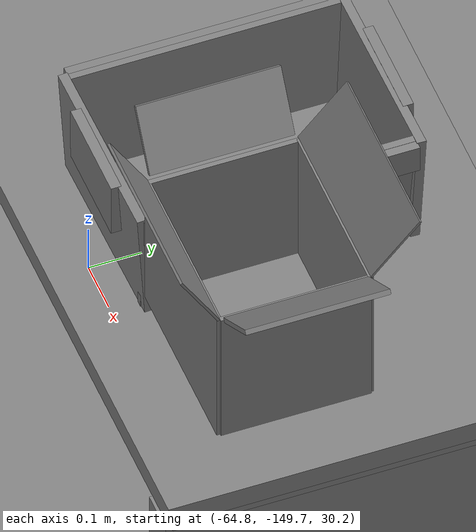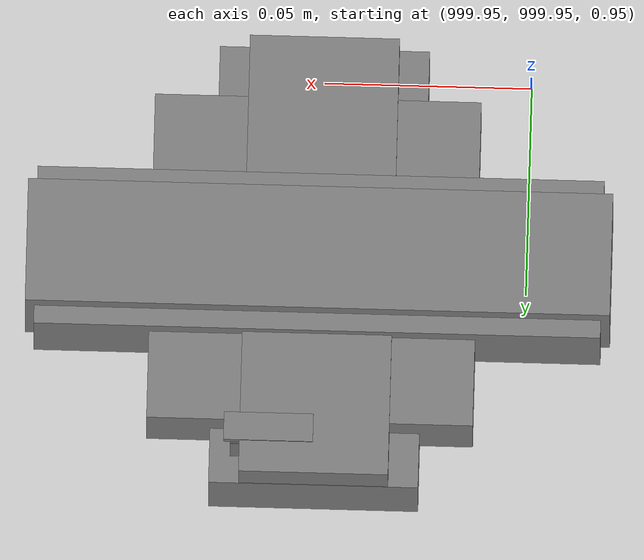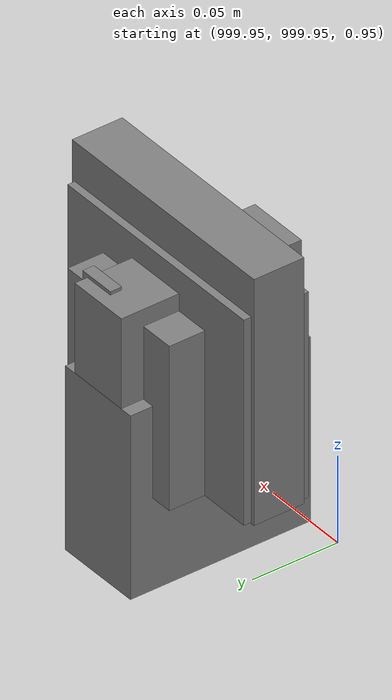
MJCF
<mujoco>
    <option gravity="0.000000000 0.000000000 -9.810000420" timestep="0.0049999999" integrator="implicitfast" density="1.225" viscosity="1.8000001e-05" noslip_iterations="10" iterations="100" sdf_iterations="50">
        <flag multiccd="disable"/>
    </option>
    <size memory="1000M"/>
    <compiler coordinate="local"/>
    <worldbody>
        <light cutoff="30" pos="0 1 1" dir="0 -1 -2"/>
        <light cutoff="30" pos="0 -1 1" dir="0 1 -2"/>
        <body pos="1000.000000000 1000.000000000 1.000000000" euler="0.000000000 0.000000000 180.000000000" name="openloong_gripper_2f85_fix_base_usda_battery_01">
            <geom contype="1" conaffinity="1" density="1000" type="box" material="" rgba="0.500000000 0.500000000 0.500000000 1.000000000" solimp="0.899999976 0.949999988 0.001000000" friction="1.000000000 0.005000000 0.000100000" solref="0.020000000 1.000000000" margin="0" condim="3" group="0" pos="-0.011123657 -0.041940309 0.101691343" quat="1.000000000 0.000000000 0.000000000 0.000000000" size="0.010800000 0.003375000 0.004725000" name="openloong_gripper_2f85_fix_base_usda_geom_140280DA_5BEB_4256_AAE0_7DEC3E3AE593"/>
            <geom contype="1" conaffinity="1" density="1000" type="box" material="" rgba="0.500000000 0.500000000 0.500000000 1.000000000" solimp="0.899999976 0.949999988 0.001000000" friction="1.000000000 0.005000000 0.000100000" solref="0.020000000 1.000000000" margin="0" condim="3" group="0" pos="-0.010876465 -0.044247437 0.047066893" quat="0.998702705 -0.050920475 0.000000000 0.000000000" size="0.009450001 0.002700000 0.024975000" name="openloong_gripper_2f85_fix_base_usda_geom_679C51E8_BC6B_47CE_B380_1DC26EAB47BC"/>
            <geom contype="1" conaffinity="1" density="1000" type="box" material="" rgba="0.500000000 0.500000000 0.500000000 1.000000000" solimp="0.899999976 0.949999988 0.001000000" friction="1.000000000 0.005000000 0.000100000" solref="0.020000000 1.000000000" margin="0" condim="3" group="0" pos="-0.001235962 -0.000659180 0.047381196" quat="1.000000000 0.000000000 0.000000000 0.000000000" size="0.039420001 0.039150000 0.047250003" name="openloong_gripper_2f85_fix_base_usda_geom_9184E545_CE03_4B5B_8B0E_704DB148C356"/>
            <geom contype="1" conaffinity="1" density="1000" type="box" material="" rgba="0.500000000 0.500000000 0.500000000 1.000000000" solimp="0.899999976 0.949999988 0.001000000" friction="1.000000000 0.005000000 0.000100000" solref="0.020000000 1.000000000" margin="0" condim="3" group="0" pos="-0.010876465 -0.039138794 0.009851727" quat="1.000000000 0.000000000 0.000000000 0.000000000" size="0.009450001 0.010800000 0.013500000" name="openloong_gripper_2f85_fix_base_usda_geom_CE997176_2A6B_4953_9FF6_7EE5AEAC8B31"/>
            <geom contype="1" conaffinity="1" density="1000" type="box" material="" rgba="0.500000000 0.500000000 0.500000000 1.000000000" solimp="0.899999976 0.949999988 0.001000000" friction="1.000000000 0.005000000 0.000100000" solref="0.020000000 1.000000000" margin="0" condim="3" group="0" pos="-0.010876465 -0.041528322 0.071508206" quat="1.000000000 0.000000000 0.000000000 0.000000000" size="0.009450001 0.002700000 0.027000001" name="openloong_gripper_2f85_fix_base_usda_geom_6802E473_2A87_4537_B76E_0BB8507E8EE6"/>
            <freejoint name="openloong_gripper_2f85_fix_base_usda_battery_01_joint"/>
            <site size="0.005000000 0.005000000 0.005000000" rgba="0.500000000 0.500000000 0.500000000 1.000000000" pos="0.000000000 0.000000000 0.000000000" quat="0.999961913 0.008726500 0.000000000 0.000000000" group="0" type="sphere" name="openloong_gripper_2f85_fix_base_usda_battery_01site"/>
        </body>
        <body pos="1000.000000000 999.999938965 1.000000000" euler="0.000000000 0.000000000 180.000000000" name="openloong_gripper_2f85_fix_base_usda_intelcore_i5">
            <geom contype="1" conaffinity="1" density="1000" type="box" material="" rgba="0.500000000 0.500000000 0.500000000 1.000000000" solimp="0.899999976 0.949999988 0.001000000" friction="1.000000000 0.005000000 0.000100000" solref="0.020000000 1.000000000" margin="0" condim="3" group="0" pos="0.000000000 0.000000000 0.051722717" quat="0.707106709 0.000000000 0.000000000 -0.707106769" size="0.052800000 0.018080002 0.052800000" name="openloong_gripper_2f85_fix_base_usda_geom_3299E5CA_D822_4FAD_9B7E_BEB787A50AE1"/>
            <freejoint name="openloong_gripper_2f85_fix_base_usda_intelcore_i5_joint"/>
            <site size="0.005000000 0.005000000 0.005000000" rgba="0.500000000 0.500000000 0.500000000 1.000000000" pos="0.000000000 0.000000000 0.000000000" quat="0.999961913 0.008726534 0.000000000 0.000000000" group="0" type="sphere" name="openloong_gripper_2f85_fix_base_usda_intelcore_i5site"/>
        </body>
        <body pos="1000.000000000 1000.000000000 1.000000000" euler="0.000000000 0.000000000 180.000000000" name="openloong_gripper_2f85_fix_base_usda_cpu_fan">
            <geom contype="1" conaffinity="1" density="1000" type="box" material="" rgba="0.500000000 0.500000000 0.500000000 1.000000000" solimp="0.899999976 0.949999988 0.001000000" friction="1.000000000 0.005000000 0.000100000" solref="0.020000000 1.000000000" margin="0" condim="3" group="0" pos="0.000000000 0.000000000 0.070034981" quat="0.000000000 0.000000000 0.000000000 1.000000000" size="0.070700005 0.014699999 0.070700005" name="openloong_gripper_2f85_fix_base_usda_geom_0B27390F_7E10_4897_AA2C_FF5049E41DD1"/>
            <freejoint name="openloong_gripper_2f85_fix_base_usda_cpu_fan_joint"/>
            <site size="0.005000000 0.005000000 0.005000000" rgba="0.500000000 0.500000000 0.500000000 1.000000000" pos="0.000000000 0.000000000 0.000000000" quat="0.999961913 0.008726535 0.000000000 0.000000000" group="0" type="sphere" name="openloong_gripper_2f85_fix_base_usda_cpu_fancsite"/>
        </body>
        <body pos="1000.000000000 1000.000000000 1.000000000" euler="0.000000000 0.000000000 180.000000000" name="openloong_gripper_2f85_fix_base_usda_wifi_box">
            <geom contype="1" conaffinity="1" density="1000" type="box" material="" rgba="0.500000000 0.500000000 0.500000000 1.000000000" solimp="0.899999976 0.949999988 0.001000000" friction="1.000000000 0.005000000 0.000100000" solref="0.020000000 1.000000000" margin="0" condim="3" group="0" pos="0.000000000 0.000000000 0.058978677" quat="0.000000000 0.000000047 0.000000000 1.000000000" size="0.068499997 0.018999999 0.059000000" name="openloong_gripper_2f85_fix_base_usda_geom_7EB405F0_0531_4AD3_B824_E97A101E5DFA"/>
            <freejoint name="openloong_gripper_2f85_fix_base_usda_wifi_box_joint"/>
            <site size="0.005000000 0.005000000 0.005000000" rgba="0.500000000 0.500000000 0.500000000 1.000000000" pos="0.000000000 0.000000000 0.000000000" quat="0.999961913 0.008726500 0.000000000 0.000000000" group="0" type="sphere" name="openloong_gripper_2f85_fix_base_usda_wifi_boxsite"/>
        </body>
        <body pos="-66.215164185 -149.572708130 31.162548065" euler="132.444381714 56.735256195 1.739143372" mocap="true" name="spotlight6_SpotLight"/>
        <body pos="1000.000000000 1000.000000000 1.000000000" euler="0.000011953 0.000005123 -179.999984741" name="openloong_gripper_2f85_fix_base_usda_intel_box">
            <geom contype="1" conaffinity="1" density="1000" type="box" material="" rgba="0.500000000 0.500000000 0.500000000 1.000000000" solimp="0.899999976 0.949999988 0.001000000" friction="1.000000000 0.005000000 0.000100000" solref="0.020000000 1.000000000" margin="0" condim="3" group="0" pos="0.000000000 -0.000067139 0.000082284" quat="0.707106709 0.000000225 0.000000253 0.707106650" size="0.052800003 0.025300000 0.052800003" name="openloong_gripper_2f85_fix_base_usda_geom_8F751776_1C9A_43DA_AD35_C2A669876ADE"/>
            <freejoint name="openloong_gripper_2f85_fix_base_usda_intel_box_joint"/>
            <site size="0.005000000 0.005000000 0.005000000" rgba="0.500000000 0.500000000 0.500000000 1.000000000" pos="0.000000000 0.000000000 0.000000000" quat="0.999961913 0.008726500 0.000000000 0.000000000" group="0" type="sphere" name="openloong_gripper_2f85_fix_base_usda_intel_boxsite"/>
        </body>
        <body pos="-66.110931396 -149.658264160 31.162879944" euler="-23.188491821 45.596836090 -85.165405273" mocap="true" name="spotlight5_SpotLight"/>
        <body pos="-65.945343018 -148.826766968 31.164258957" euler="-104.374069214 24.151601791 -18.875196457" mocap="true" name="spotlight1_SpotLight"/>
        <body pos="-64.866622925 -149.383972168 30.183746338" euler="89.999984741 89.999946594 0.000000000" name="openloong_gripper_2f85_fix_base_usda_bluebox_01">
            <geom contype="1" conaffinity="1" density="1000" type="box" material="" rgba="0.500000000 0.500000000 0.500000000 1.000000000" solimp="0.899999976 0.949999988 0.001000000" friction="1.000000000 0.005000000 0.000100000" solref="0.020000000 1.000000000" margin="0" condim="3" group="0" pos="0.276580811 0.187225342 0.000068665" quat="0.707106948 0.000077471 0.707106352 0.000077486" size="0.100000001 0.057999998 0.010000000" name="openloong_gripper_2f85_fix_base_usda_geom_C2B7DD01_E18A_4F4E_8BC1_5BF2ABDF27AA"/>
            <geom contype="1" conaffinity="1" density="1000" type="box" material="" rgba="0.500000000 0.500000000 0.500000000 1.000000000" solimp="0.899999976 0.949999988 0.001000000" friction="1.000000000 0.005000000 0.000100000" solref="0.020000000 1.000000000" margin="0" condim="3" group="0" pos="0.000000000 0.002883911 0.000000000" quat="0.999999881 0.000000000 0.000000000 0.000000000" size="0.254000008 0.003000000 0.172000006" name="openloong_gripper_2f85_fix_base_usda_geom_D2EEA1CB_5F57_4BAE_BFD8_3AB82F4E6561"/>
            <geom contype="1" conaffinity="1" density="1000" type="box" material="" rgba="0.500000000 0.500000000 0.500000000 1.000000000" solimp="0.899999976 0.949999988 0.001000000" friction="1.000000000 0.005000000 0.000100000" solref="0.020000000 1.000000000" margin="0" condim="3" group="0" pos="0.000000000 0.124874115 0.173484802" quat="0.999796331 0.020176515 -0.000000015 0.000000030" size="0.259999990 0.119999997 0.007000000" name="openloong_gripper_2f85_fix_base_usda_geom_02F24E7B_9614_480C_9EAA_2E02CC00F112"/>
            <geom contype="1" conaffinity="1" density="1000" type="box" material="" rgba="0.500000000 0.500000000 0.500000000 1.000000000" solimp="0.899999976 0.949999988 0.001000000" friction="1.000000000 0.005000000 0.000100000" solref="0.020000000 1.000000000" margin="0" condim="3" group="0" pos="0.000000000 0.124874115 -0.173469543" quat="0.999796331 -0.020176545 -0.000000015 0.000000000" size="0.259999990 0.119999997 0.007000000" name="openloong_gripper_2f85_fix_base_usda_geom_64883813_940F_4D0E_B354_CE56A6F99913"/>
            <geom contype="1" conaffinity="1" density="1000" type="box" material="" rgba="0.500000000 0.500000000 0.500000000 1.000000000" solimp="0.899999976 0.949999988 0.001000000" friction="1.000000000 0.005000000 0.000100000" solref="0.020000000 1.000000000" margin="0" condim="3" group="0" pos="0.000000000 0.214008331 0.188980103" quat="0.999912977 0.013176724 0.000000015 0.000000000" size="0.259999990 0.029999999 0.012500000" name="openloong_gripper_2f85_fix_base_usda_geom_D630643C_9367_4695_AFC9_CD8BFD12F6BA"/>
            <geom contype="1" conaffinity="1" density="1000" type="box" material="" rgba="0.500000000 0.500000000 0.500000000 1.000000000" solimp="0.899999976 0.949999988 0.001000000" friction="1.000000000 0.005000000 0.000100000" solref="0.020000000 1.000000000" margin="0" condim="3" group="0" pos="-0.258361816 0.125289917 0.001876831" quat="0.702796936 -0.020792112 0.710783124 0.020769298" size="0.189999998 0.119999997 0.009000000" name="openloong_gripper_2f85_fix_base_usda_geom_CC57F8DA_D059_475F_9119_06BBA90DBD5B"/>
            <geom contype="1" conaffinity="1" density="1000" type="box" material="" rgba="0.500000000 0.500000000 0.500000000 1.000000000" solimp="0.899999976 0.949999988 0.001000000" friction="1.000000000 0.005000000 0.000100000" solref="0.020000000 1.000000000" margin="0" condim="3" group="0" pos="0.000000000 0.214008331 -0.188980103" quat="0.999912977 -0.013176769 0.000000030 0.000000015" size="0.259999990 0.029999999 0.012500000" name="openloong_gripper_2f85_fix_base_usda_geom_BFEFED9C_D2F3_4485_8179_FF30B8A4A9EF"/>
            <geom contype="1" conaffinity="1" density="1000" type="box" material="" rgba="0.500000000 0.500000000 0.500000000 1.000000000" solimp="0.899999976 0.949999988 0.001000000" friction="1.000000000 0.005000000 0.000100000" solref="0.020000000 1.000000000" margin="0" condim="3" group="0" pos="-0.276611328 0.187225342 0.000068665" quat="0.707106650 0.000077441 0.707106709 0.000077456" size="0.100000001 0.057999998 0.010000000" name="openloong_gripper_2f85_fix_base_usda_geom_A8AFEBE0_0FCD_4550_B664_3F6B765982C3"/>
            <geom contype="1" conaffinity="1" density="1000" type="box" material="" rgba="0.500000000 0.500000000 0.500000000 1.000000000" solimp="0.899999976 0.949999988 0.001000000" friction="1.000000000 0.005000000 0.000100000" solref="0.020000000 1.000000000" margin="0" condim="3" group="0" pos="0.258331299 0.125289917 0.001876831" quat="0.702851415 0.018856421 0.710823774 -0.019329369" size="0.189999998 0.119999997 0.009000000" name="openloong_gripper_2f85_fix_base_usda_geom_79F6847A_2AA0_4883_91E3_BBB775D5190D"/>
            <freejoint name="openloong_gripper_2f85_fix_base_usda_bluebox_01_joint"/>
            <site size="0.005000000 0.005000000 0.005000000" rgba="0.500000000 0.500000000 0.500000000 1.000000000" pos="0.000000000 0.000000000 0.000000000" quat="0.999961913 0.008726534 0.000000000 0.000000000" group="0" type="sphere" name="openloong_gripper_2f85_fix_base_usda_bluebox_01site"/>
        </body>
        <body pos="-64.496299744 -149.491867065 30.235729218" euler="0.000000000 0.000000000 89.999946594" name="openloong_gripper_2f85_fix_base_usda_cardboardbox_01">
            <geom contype="1" conaffinity="1" density="1000" type="box" material="" rgba="0.500000000 0.500000000 0.500000000 1.000000000" solimp="0.899999976 0.949999988 0.001000000" friction="1.000000000 0.005000000 0.000100000" solref="0.020000000 1.000000000" margin="0" condim="3" group="0" pos="-0.003166199 -0.004086494 0.005052090" quat="1.000000000 0.000000000 0.000000000 0.000000000" size="0.142499998 0.177500010 0.005000000" name="openloong_gripper_2f85_fix_base_usda_geom_38562FC4_2F29_49DE_8C53_EB19034539FF"/>
            <geom contype="1" conaffinity="1" density="1000" type="box" material="" rgba="0.500000000 0.500000000 0.500000000 1.000000000" solimp="0.899999976 0.949999988 0.001000000" friction="1.000000000 0.005000000 0.000100000" solref="0.020000000 1.000000000" margin="0" condim="3" group="0" pos="-0.003166199 0.170316696 0.150570869" quat="1.000000000 0.000000000 0.000000000 0.000000000" size="0.142499998 0.005000000 0.149999991" name="openloong_gripper_2f85_fix_base_usda_geom_25CB13C3_08A2_4BE3_B0B0_68BAD550A97D"/>
            <geom contype="1" conaffinity="1" density="1000" type="box" material="" rgba="0.500000000 0.500000000 0.500000000 1.000000000" solimp="0.899999976 0.949999988 0.001000000" friction="1.000000000 0.005000000 0.000100000" solref="0.020000000 1.000000000" margin="0" condim="3" group="0" pos="-0.147399902 -0.005307198 0.150570869" quat="1.000000000 0.000000000 0.000000000 0.000000000" size="0.005000000 0.177500010 0.149999991" name="openloong_gripper_2f85_fix_base_usda_geom_62136361_BDE3_426F_B0E6_3317A9F9E9D5"/>
            <geom contype="1" conaffinity="1" density="1000" type="box" material="" rgba="0.500000000 0.500000000 0.500000000 1.000000000" solimp="0.899999976 0.949999988 0.001000000" friction="1.000000000 0.005000000 0.000100000" solref="0.020000000 1.000000000" margin="0" condim="3" group="0" pos="0.140275955 -0.005307198 0.150570869" quat="1.000000000 0.000000000 0.000000000 0.000000000" size="0.005000000 0.177500010 0.149999991" name="openloong_gripper_2f85_fix_base_usda_geom_65758EF8_AC01_4CDD_A73B_9B8D8C57E4F0"/>
            <geom contype="1" conaffinity="1" density="1000" type="box" material="" rgba="0.500000000 0.500000000 0.500000000 1.000000000" solimp="0.899999976 0.949999988 0.001000000" friction="1.000000000 0.005000000 0.000100000" solref="0.020000000 1.000000000" margin="0" condim="3" group="0" pos="-0.003166199 -0.181550980 0.150570869" quat="1.000000000 0.000000000 0.000000000 0.000000000" size="0.142499998 0.005000000 0.149999991" name="openloong_gripper_2f85_fix_base_usda_geom_00A27D78_DF66_42A3_83E7_10B85976D04E"/>
            <freejoint name="openloong_gripper_2f85_fix_base_usda_cardboardbox_01_joint"/>
            <site size="0.005000000 0.005000000 0.005000000" rgba="0.500000000 0.500000000 0.500000000 1.000000000" pos="0.000000000 0.000000000 0.000000000" quat="0.999961913 0.008726535 0.000000000 0.000000000" group="0" type="sphere" name="openloong_gripper_2f85_fix_base_usda_site_91DA06E2_3887_4EBA_8702_56C0E4BF8E8F"/>
            <body pos="0.139160156 -0.004048347 0.301930904" euler="-179.999954224 49.383502960 179.999954224" name="openloong_gripper_2f85_fix_base_usda_A1_006">
                <geom contype="1" conaffinity="1" density="1000" type="box" material="" rgba="0.500000000 0.500000000 0.500000000 1.000000000" solimp="0.899999976 0.949999988 0.001000000" friction="1.000000000 0.005000000 0.000100000" solref="0.020000000 1.000000000" margin="0" condim="3" group="0" pos="-0.071587563 0.000009537 0.001745224" quat="0.999999881 0.000000000 0.000000000 0.000000000" size="0.071249999 0.179999992 0.002500000" name="openloong_gripper_2f85_fix_base_usda_geom_F7976DEF_3C78_4F37_9C0F_96738C73DEDE"/>
                <joint armature="0" stiffness="0.07" damping="0.0099999998" axis="0.000000 1.000000 0.000000" type="hinge" name="openloong_gripper_2f85_fix_base_usda_A1_006"/>
            </body>
            <body pos="-0.145902634 -0.004086494 0.301938057" euler="-180.000000000 -60.000011444 -180.000000000" name="openloong_gripper_2f85_fix_base_usda_A2_006">
                <geom contype="1" conaffinity="1" density="1000" type="box" material="" rgba="0.500000000 0.500000000 0.500000000 1.000000000" solimp="0.899999976 0.949999988 0.001000000" friction="1.000000000 0.005000000 0.000100000" solref="0.020000000 1.000000000" margin="0" condim="3" group="0" pos="0.071268082 0.000009537 0.002717972" quat="0.000002921 0.000000000 -0.000000030 0.999999881" size="0.071249999 0.179999992 0.002500000" name="openloong_gripper_2f85_fix_base_usda_geom_B145EB46_6B4E_4B26_8F91_7ECB6BE6B851"/>
                <joint armature="0" stiffness="0.07" damping="0.0099999998" axis="0.000000 1.000000 0.000000" type="hinge" name="openloong_gripper_2f85_fix_base_usda_A2_006"/>
            </body>
            <body pos="-0.003385544 0.175991058 0.301930904" euler="-125.858116150 -0.000004561 0.000002331" name="openloong_gripper_2f85_fix_base_usda_B2_006">
                <geom contype="1" conaffinity="1" density="1000" type="box" material="" rgba="0.500000000 0.500000000 0.500000000 1.000000000" solimp="0.899999976 0.949999988 0.001000000" friction="1.000000000 0.005000000 0.000100000" solref="0.020000000 1.000000000" margin="0" condim="3" group="0" pos="0.000009537 -0.070939064 -0.002470016" quat="0.999614120 0.027776197 -0.000000015 0.000000030" size="0.137500003 0.064999998 0.005000000" name="openloong_gripper_2f85_fix_base_usda_geom_F18061AA_B91C_4282_8EE8_D830883DFD20"/>
                <joint armature="0" stiffness="0.07" damping="0.0099999998" axis="1.000000 0.000000 0.000000" type="hinge" name="openloong_gripper_2f85_fix_base_usda_B2_006"/>
            </body>
            <body pos="-0.003385544 -0.184140205 0.301938057" euler="147.805557251 0.000000000 0.000000000" name="openloong_gripper_2f85_fix_base_usda_B1_006">
                <geom contype="1" conaffinity="1" density="1000" type="box" material="" rgba="0.500000000 0.500000000 0.500000000 1.000000000" solimp="0.899999976 0.949999988 0.001000000" friction="1.000000000 0.005000000 0.000100000" solref="0.020000000 1.000000000" margin="0" condim="3" group="0" pos="-0.000028610 0.070202351 -0.002703667" quat="0.999614179 -0.027776167 0.000000000 0.000000000" size="0.137500003 0.064999998 0.005000000" name="openloong_gripper_2f85_fix_base_usda_geom_DB2E3151_750C_4E76_AA48_4D96C75B18EE"/>
                <joint armature="0" stiffness="0.07" damping="0.0099999998" axis="1.000000 0.000000 0.000000" type="hinge" name="openloong_gripper_2f85_fix_base_usda_B1_006"/>
            </body>
        </body>
        <body pos="-65.882858276 -149.481979370 30.229999542" euler="-64.487716675 0.000000000 0.000000000" name="openloong_gripper_2f85_fix_base_usda_Barcode">
            <geom contype="1" conaffinity="1" density="1000" type="box" material="" rgba="0.500000000 0.500000000 0.500000000 1.000000000" solimp="0.899999976 0.949999988 0.001000000" friction="1.000000000 0.005000000 0.000100000" solref="0.020000000 1.000000000" margin="0" condim="3" group="0" pos="0.000000000 0.013038635 0.001419067" quat="0.000000000 0.000000000 0.000000000 1.000000119" size="0.034000002 0.010000000 0.017999999" name="openloong_gripper_2f85_fix_base_usda_geom_D33338E3_1374_45F2_B1DD_6D7BAE66AAC3"/>
            <geom contype="1" conaffinity="1" density="1000" type="box" material="" rgba="0.500000000 0.500000000 0.500000000 1.000000000" solimp="0.899999976 0.949999988 0.001000000" friction="1.000000000 0.005000000 0.000100000" solref="0.020000000 1.000000000" margin="0" condim="3" group="0" pos="0.000000000 -0.035301208 -0.007095337" quat="0.000000000 0.000000000 -0.043619365 0.999048233" size="0.028999999 0.010000000 0.020000000" name="openloong_gripper_2f85_fix_base_usda_geom_29631FEF_341F_4E8E_8678_BBBD44762FCA"/>
            <geom contype="1" conaffinity="1" density="1000" type="box" material="" rgba="0.500000000 0.500000000 0.500000000 1.000000000" solimp="0.899999976 0.949999988 0.001000000" friction="1.000000000 0.005000000 0.000100000" solref="0.020000000 1.000000000" margin="0" condim="3" group="0" pos="0.000000000 -0.043411255 -0.011749268" quat="0.922262907 0.386563420 0.000000000 0.000000000" size="0.026000001 0.010000000 0.020000000" name="openloong_gripper_2f85_fix_base_usda_geom_F5D1D22E_0563_4B1A_A783_C0C86BF6E495"/>
            <geom contype="1" conaffinity="1" density="1000" type="box" material="" rgba="0.500000000 0.500000000 0.500000000 1.000000000" solimp="0.899999976 0.949999988 0.001000000" friction="1.000000000 0.005000000 0.000100000" solref="0.020000000 1.000000000" margin="0" condim="3" group="0" pos="0.000000000 -0.016967773 -0.031860352" quat="0.000000000 0.000000000 0.000000000 1.000000119" size="0.008000000 0.010000000 0.013000000" name="openloong_gripper_2f85_fix_base_usda_geom_3D078577_FBF7_490C_9400_E2A298A3B7F8"/>
            <geom contype="1" conaffinity="1" density="1000" type="box" material="" rgba="0.500000000 0.500000000 0.500000000 1.000000000" solimp="0.899999976 0.949999988 0.001000000" friction="1.000000000 0.005000000 0.000100000" solref="0.020000000 1.000000000" margin="0" condim="3" group="0" pos="0.000000000 -0.001869202 0.000312805" quat="0.953716993 0.300705761 0.000000000 0.000000000" size="0.032000002 0.010000000 0.018999999" name="openloong_gripper_2f85_fix_base_usda_geom_014A9756_1A21_404E_8E9C_5E1A3385E3BE"/>
            <geom contype="1" conaffinity="1" density="1000" type="box" material="" rgba="0.500000000 0.500000000 0.500000000 1.000000000" solimp="0.899999976 0.949999988 0.001000000" friction="1.000000000 0.005000000 0.000100000" solref="0.020000000 1.000000000" margin="0" condim="3" group="0" pos="0.000000000 -0.019531250 -0.003173828" quat="0.953716993 0.300705761 0.000000000 0.000000000" size="0.030999999 0.010000000 0.020000000" name="openloong_gripper_2f85_fix_base_usda_geom_5398AC93_5FD4_4A9B_BE3D_955C14B7C4C8"/>
            <geom contype="1" conaffinity="1" density="1000" type="box" material="" rgba="0.500000000 0.500000000 0.500000000 1.000000000" solimp="0.899999976 0.949999988 0.001000000" friction="1.000000000 0.005000000 0.000100000" solref="0.020000000 1.000000000" margin="0" condim="3" group="0" pos="0.000000000 -0.035301208 -0.007095337" quat="0.953716993 0.300705761 0.000000000 0.000000000" size="0.028999999 0.010000000 0.020000000" name="openloong_gripper_2f85_fix_base_usda_geom_EFAB8AF1_861D_46A6_89F8_3A2B588CEDA0"/>
            <geom contype="1" conaffinity="1" density="1000" type="box" material="" rgba="0.500000000 0.500000000 0.500000000 1.000000000" solimp="0.899999976 0.949999988 0.001000000" friction="1.000000000 0.005000000 0.000100000" solref="0.020000000 1.000000000" margin="0" condim="3" group="0" pos="0.000000000 -0.042617798 -0.071121216" quat="0.000000000 0.000000000 0.000000000 1.000000119" size="0.013000000 0.021000000 0.059999999" name="openloong_gripper_2f85_fix_base_usda_geom_20776803_6CD5_4307_AC3B_B558F7613CBE"/>
            <freejoint name="openloong_gripper_2f85_fix_base_usda_Barcode_joint"/>
            <site size="0.005000000 0.005000000 0.005000000" rgba="0.500000000 0.500000000 0.500000000 1.000000000" pos="0.000000000 0.000000000 0.000000000" quat="1.000000000 0.000000000 0.000000000 0.000000000" group="0" type="sphere" name="openloong_gripper_2f85_fix_base_usda_Barcode_site"/>
        </body>
        <body pos="-66.745018005 -149.392349243 30.184000015" euler="0.000000000 0.000000000 89.999946594" name="[22330472958960]_Basket_01">
            <geom contype="1" conaffinity="1" density="1000" type="box" material="" rgba="0.500000000 0.500000000 0.500000000 1.000000000" solimp="0.899999976 0.949999988 0.001000000" friction="1.000000000 0.005000000 0.000100000" solref="0.020000000 1.000000000" margin="0" condim="3" group="0" pos="-0.052425385 0.389207840 0.089787483" quat="0.707107008 0.000000000 0.000000000 0.707106411" size="0.014249999 0.014249999 0.059999999" name="[22330472958960]_geom_B5D1E10E_840A_4924_B00A_438444F1CBA2"/>
            <geom contype="1" conaffinity="1" density="1000" type="box" material="" rgba="0.500000000 0.500000000 0.500000000 1.000000000" solimp="0.899999976 0.949999988 0.001000000" friction="1.000000000 0.005000000 0.000100000" solref="0.020000000 1.000000000" margin="0" condim="3" group="0" pos="0.264015198 -0.133043289 0.089787483" quat="0.707107008 0.000000000 0.000000000 0.707106411" size="0.014249999 0.014249999 0.059999999" name="[22330472958960]_geom_CFEFFB65_740B_4C7E_B08E_32DD1AA7F8D9"/>
            <geom contype="1" conaffinity="1" density="1000" type="box" material="" rgba="0.500000000 0.500000000 0.500000000 1.000000000" solimp="0.899999976 0.949999988 0.001000000" friction="1.000000000 0.005000000 0.000100000" solref="0.020000000 1.000000000" margin="0" condim="3" group="0" pos="-0.264015198 -0.265548706 0.089793205" quat="0.707107008 0.000000000 0.000000000 0.707106411" size="0.014249999 0.014249999 0.059999999" name="[22330472958960]_geom_86C85114_3D5A_4FDF_903D_4DE51CB57D4A"/>
            <geom contype="1" conaffinity="1" density="1000" type="box" material="" rgba="0.500000000 0.500000000 0.500000000 1.000000000" solimp="0.899999976 0.949999988 0.001000000" friction="1.000000000 0.005000000 0.000100000" solref="0.020000000 1.000000000" margin="0" condim="3" group="0" pos="-0.160263062 -0.389322281 0.089793205" quat="0.707107008 0.000000000 0.000000000 0.707106411" size="0.014249999 0.014249999 0.059999999" name="[22330472958960]_geom_6DCCD9F6_5FDC_4198_B505_5B8B3826856F"/>
            <geom contype="1" conaffinity="1" density="1000" type="box" material="" rgba="0.500000000 0.500000000 0.500000000 1.000000000" solimp="0.899999976 0.949999988 0.001000000" friction="1.000000000 0.005000000 0.000100000" solref="0.020000000 1.000000000" margin="0" condim="3" group="0" pos="0.162265778 -0.389322281 0.089787483" quat="0.707107008 0.000000000 0.000000000 0.707106411" size="0.014249999 0.014249999 0.059999999" name="[22330472958960]_geom_E655D2D7_26A3_4924_B741_965EC9D30B30"/>
            <geom contype="1" conaffinity="1" density="1000" type="box" material="" rgba="0.500000000 0.500000000 0.500000000 1.000000000" solimp="0.899999976 0.949999988 0.001000000" friction="1.000000000 0.005000000 0.000100000" solref="0.020000000 1.000000000" margin="0" condim="3" group="0" pos="0.264015198 0.389207840 0.089787483" quat="0.707107008 0.000000000 0.000000000 0.707106411" size="0.014249999 0.014249999 0.059999999" name="[22330472958960]_geom_EBDCFBDB_0116_4255_A6F9_A67C99D253C1"/>
            <geom contype="1" conaffinity="1" density="1000" type="box" material="" rgba="0.500000000 0.500000000 0.500000000 1.000000000" solimp="0.899999976 0.949999988 0.001000000" friction="1.000000000 0.005000000 0.000100000" solref="0.020000000 1.000000000" margin="0" condim="3" group="0" pos="-0.264015198 -0.133043289 0.089793205" quat="0.707107008 0.000000000 0.000000000 0.707106411" size="0.014249999 0.014249999 0.059999999" name="[22330472958960]_geom_96F31576_D8C5_49A5_A78A_AD29411F57E5"/>
            <geom contype="1" conaffinity="1" density="1000" type="box" material="" rgba="0.500000000 0.500000000 0.500000000 1.000000000" solimp="0.899999976 0.949999988 0.001000000" friction="1.000000000 0.005000000 0.000100000" solref="0.020000000 1.000000000" margin="0" condim="3" group="0" pos="-0.264026642 0.269256592 0.089793205" quat="0.707107008 0.000000000 0.000000000 0.707106411" size="0.014249999 0.014249999 0.059999999" name="[22330472958960]_geom_9E20A89F_C0AB_48CA_8D01_15FECB7B6DEE"/>
            <geom contype="1" conaffinity="1" density="1000" type="box" material="" rgba="0.500000000 0.500000000 0.500000000 1.000000000" solimp="0.899999976 0.949999988 0.001000000" friction="1.000000000 0.005000000 0.000100000" solref="0.020000000 1.000000000" margin="0" condim="3" group="0" pos="0.054462433 0.389207840 0.089787483" quat="0.707107008 0.000000000 0.000000000 0.707106411" size="0.014249999 0.014249999 0.059999999" name="[22330472958960]_geom_7B255E51_FC70_41B7_8A45_E8F551ACE1E7"/>
            <geom contype="1" conaffinity="1" density="1000" type="box" material="" rgba="0.500000000 0.500000000 0.500000000 1.000000000" solimp="0.899999976 0.949999988 0.001000000" friction="1.000000000 0.005000000 0.000100000" solref="0.020000000 1.000000000" margin="0" condim="3" group="0" pos="0.054462433 -0.389322281 0.089787483" quat="0.707107008 0.000000000 0.000000000 0.707106411" size="0.014249999 0.014249999 0.059999999" name="[22330472958960]_geom_7E9A058F_C8ED_4CF9_94E5_837912C3D3BD"/>
            <geom contype="1" conaffinity="1" density="1000" type="box" material="" rgba="0.500000000 0.500000000 0.500000000 1.000000000" solimp="0.899999976 0.949999988 0.001000000" friction="1.000000000 0.005000000 0.000100000" solref="0.020000000 1.000000000" margin="0" condim="3" group="0" pos="0.264015198 0.269256592 0.089793205" quat="0.707107008 0.000000000 0.000000000 0.707106411" size="0.014249999 0.014249999 0.059999999" name="[22330472958960]_geom_22CFF354_67BC_4220_9725_414A22EFEDFB"/>
            <geom contype="1" conaffinity="1" density="1000" type="box" material="" rgba="0.500000000 0.500000000 0.500000000 1.000000000" solimp="0.899999976 0.949999988 0.001000000" friction="1.000000000 0.005000000 0.000100000" solref="0.020000000 1.000000000" margin="0" condim="3" group="0" pos="0.264015198 -0.389322281 0.089787483" quat="0.707107008 0.000000000 0.000000000 0.707106411" size="0.014249999 0.014249999 0.059999999" name="[22330472958960]_geom_F026C33B_D2A9_439C_A4D9_4252CC24AFB2"/>
            <geom contype="1" conaffinity="1" density="1000" type="box" material="" rgba="0.500000000 0.500000000 0.500000000 1.000000000" solimp="0.899999976 0.949999988 0.001000000" friction="1.000000000 0.005000000 0.000100000" solref="0.020000000 1.000000000" margin="0" condim="3" group="0" pos="0.000000000 0.000000000 0.015998840" quat="0.707107008 0.000000000 0.000000000 0.707106411" size="0.403499991 0.279000014 0.015750000" name="[22330472958960]_geom_38F2879C_D5BF_4B5F_8B36_3022A04ADB6C"/>
            <geom contype="1" conaffinity="1" density="1000" type="box" material="" rgba="0.500000000 0.500000000 0.500000000 1.000000000" solimp="0.899999976 0.949999988 0.001000000" friction="1.000000000 0.005000000 0.000100000" solref="0.020000000 1.000000000" margin="0" condim="3" group="0" pos="0.000000000 -0.389476776 0.163619041" quat="0.707107008 0.000000000 0.000000000 0.707106411" size="0.015000000 0.277500004 0.015750000" name="[22330472958960]_geom_ACD55341_1005_417F_B4F1_0C57808FD93A"/>
            <geom contype="1" conaffinity="1" density="1000" type="box" material="" rgba="0.500000000 0.500000000 0.500000000 1.000000000" solimp="0.899999976 0.949999988 0.001000000" friction="1.000000000 0.005000000 0.000100000" solref="0.020000000 1.000000000" margin="0" condim="3" group="0" pos="0.162265778 0.389207840 0.089787483" quat="0.707107008 0.000000000 0.000000000 0.707106411" size="0.014249999 0.014249999 0.059999999" name="[22330472958960]_geom_1672425C_C750_410D_901F_C713C08FBA32"/>
            <geom contype="1" conaffinity="1" density="1000" type="box" material="" rgba="0.500000000 0.500000000 0.500000000 1.000000000" solimp="0.899999976 0.949999988 0.001000000" friction="1.000000000 0.005000000 0.000100000" solref="0.020000000 1.000000000" margin="0" condim="3" group="0" pos="0.000000000 0.389471054 0.163619041" quat="0.707107008 0.000000000 0.000000000 0.707106411" size="0.015000000 0.277500004 0.015750000" name="[22330472958960]_geom_BA2DC1C2_93FD_4442_B016_6A263EDE2568"/>
            <geom contype="1" conaffinity="1" density="1000" type="box" material="" rgba="0.500000000 0.500000000 0.500000000 1.000000000" solimp="0.899999976 0.949999988 0.001000000" friction="1.000000000 0.005000000 0.000100000" solref="0.020000000 1.000000000" margin="0" condim="3" group="0" pos="-0.263511658 0.000000000 0.163619041" quat="0.707107008 0.000000000 0.000000000 0.707106411" size="0.403499991 0.015000000 0.015750000" name="[22330472958960]_geom_77B883A2_CE17_4931_B9EA_A41F24C68E07"/>
            <geom contype="1" conaffinity="1" density="1000" type="box" material="" rgba="0.500000000 0.500000000 0.500000000 1.000000000" solimp="0.899999976 0.949999988 0.001000000" friction="1.000000000 0.005000000 0.000100000" solref="0.020000000 1.000000000" margin="0" condim="3" group="0" pos="-0.264015198 0.141334534 0.089793205" quat="0.707107008 0.000000000 0.000000000 0.707106411" size="0.014249999 0.014249999 0.059999999" name="[22330472958960]_geom_A5ABE163_ADB0_4EFB_93B6_5750B7BB2857"/>
            <geom contype="1" conaffinity="1" density="1000" type="box" material="" rgba="0.500000000 0.500000000 0.500000000 1.000000000" solimp="0.899999976 0.949999988 0.001000000" friction="1.000000000 0.005000000 0.000100000" solref="0.020000000 1.000000000" margin="0" condim="3" group="0" pos="0.264015198 -0.265548706 0.089787483" quat="0.707107008 0.000000000 0.000000000 0.707106411" size="0.014249999 0.014249999 0.059999999" name="[22330472958960]_geom_31C804C1_9CC4_489B_AD1F_772017092207"/>
            <geom contype="1" conaffinity="1" density="1000" type="box" material="" rgba="0.500000000 0.500000000 0.500000000 1.000000000" solimp="0.899999976 0.949999988 0.001000000" friction="1.000000000 0.005000000 0.000100000" solref="0.020000000 1.000000000" margin="0" condim="3" group="0" pos="-0.160263062 0.389207840 0.089787483" quat="0.707107008 0.000000000 0.000000000 0.707106411" size="0.014249999 0.014249999 0.059999999" name="[22330472958960]_geom_0900814F_B5E6_4A39_B17F_7DDFB271F347"/>
            <geom contype="1" conaffinity="1" density="1000" type="box" material="" rgba="0.500000000 0.500000000 0.500000000 1.000000000" solimp="0.899999976 0.949999988 0.001000000" friction="1.000000000 0.005000000 0.000100000" solref="0.020000000 1.000000000" margin="0" condim="3" group="0" pos="-0.052425385 -0.389322281 0.089787483" quat="0.707107008 0.000000000 0.000000000 0.707106411" size="0.014249999 0.014249999 0.059999999" name="[22330472958960]_geom_19D49299_D040_4C32_8626_5E82230ED01D"/>
            <geom contype="1" conaffinity="1" density="1000" type="box" material="" rgba="0.500000000 0.500000000 0.500000000 1.000000000" solimp="0.899999976 0.949999988 0.001000000" friction="1.000000000 0.005000000 0.000100000" solref="0.020000000 1.000000000" margin="0" condim="3" group="0" pos="-0.264026642 -0.389322281 0.089793205" quat="0.707107008 0.000000000 0.000000000 0.707106411" size="0.014249999 0.014249999 0.059999999" name="[22330472958960]_geom_9784BCB6_EECF_4722_B569_683BB8F36A56"/>
            <geom contype="1" conaffinity="1" density="1000" type="box" material="" rgba="0.500000000 0.500000000 0.500000000 1.000000000" solimp="0.899999976 0.949999988 0.001000000" friction="1.000000000 0.005000000 0.000100000" solref="0.020000000 1.000000000" margin="0" condim="3" group="0" pos="0.264015198 0.141334534 0.089787483" quat="0.707107008 0.000000000 0.000000000 0.707106411" size="0.014249999 0.014249999 0.059999999" name="[22330472958960]_geom_BCFB2519_016A_4CCB_A517_BB6EA5A96B5F"/>
            <geom contype="1" conaffinity="1" density="1000" type="box" material="" rgba="0.500000000 0.500000000 0.500000000 1.000000000" solimp="0.899999976 0.949999988 0.001000000" friction="1.000000000 0.005000000 0.000100000" solref="0.020000000 1.000000000" margin="0" condim="3" group="0" pos="-0.264015198 0.389207840 0.089793205" quat="0.707107008 0.000000000 0.000000000 0.707106411" size="0.014249999 0.014249999 0.059999999" name="[22330472958960]_geom_06DD0832_8B7F_409E_A435_A7EDC0E4A06E"/>
            <geom contype="1" conaffinity="1" density="1000" type="box" material="" rgba="0.500000000 0.500000000 0.500000000 1.000000000" solimp="0.899999976 0.949999988 0.001000000" friction="1.000000000 0.005000000 0.000100000" solref="0.020000000 1.000000000" margin="0" condim="3" group="0" pos="0.264015198 0.004480362 0.089787483" quat="0.707107008 0.000000000 0.000000000 0.707106411" size="0.014249999 0.014249999 0.059999999" name="[22330472958960]_geom_89A264E2_87C2_4E42_B724_97F2F4174E77"/>
            <geom contype="1" conaffinity="1" density="1000" type="box" material="" rgba="0.500000000 0.500000000 0.500000000 1.000000000" solimp="0.899999976 0.949999988 0.001000000" friction="1.000000000 0.005000000 0.000100000" solref="0.020000000 1.000000000" margin="0" condim="3" group="0" pos="0.263694763 -0.000011444 0.163619041" quat="0.707107008 0.000000000 0.000000000 0.707106411" size="0.403499991 0.015000000 0.015750000" name="[22330472958960]_geom_0AE80FD7_6079_464F_9B21_51E16398A8BB"/>
            <geom contype="1" conaffinity="1" density="1000" type="box" material="" rgba="0.500000000 0.500000000 0.500000000 1.000000000" solimp="0.899999976 0.949999988 0.001000000" friction="1.000000000 0.005000000 0.000100000" solref="0.020000000 1.000000000" margin="0" condim="3" group="0" pos="-0.264015198 0.004480362 0.089793205" quat="0.707107008 0.000000000 0.000000000 0.707106411" size="0.014249999 0.014249999 0.059999999" name="[22330472958960]_geom_9C315835_5A1D_455A_A3D7_27EA768EB378"/>
            <freejoint name="[22330472958960]_joint_D25702B5_5CA2_4447_98DA_8187344A3256"/>
        </body>
        <body pos="0.000000000 0.000000000 0.000000000" euler="0.000000000 0.000000000 0.000000000" name="Static Objects_Static Objects">
            <geom contype="1" conaffinity="1" density="1000" type="box" material="" rgba="0.500000000 0.500000000 0.500000000 1.000000000" solimp="0.899999976 0.949999988 0.001000000" friction="1.000000000 0.005000000 0.000100000" solref="0.020000000 1.000000000" margin="0" condim="3" group="0" pos="-67.544113159 -149.365814209 29.727830887" quat="0.500000417 0.499999970 0.499999553 0.499999970" size="0.381000012 0.319999993 0.041000001" name="Static Objects_geom_97763DD2_BE43_457D_AB34_3729E9F1E293"/>
            <geom contype="1" conaffinity="1" density="1000" type="box" material="" rgba="0.500000000 0.500000000 0.500000000 1.000000000" solimp="0.899999976 0.949999988 0.001000000" friction="1.000000000 0.005000000 0.000100000" solref="0.020000000 1.000000000" margin="0" condim="3" group="0" pos="-68.239501953 -149.365814209 30.086868286" quat="0.500000417 0.499999970 0.499999553 0.499999970" size="0.370999992 0.039500002 0.745000005" name="Static Objects_geom_4A60627B_7B04_48E7_89B1_0CD75AC1C8F1"/>
            <geom contype="1" conaffinity="1" density="1000" type="box" material="" rgba="0.500000000 0.500000000 0.500000000 1.000000000" solimp="0.899999976 0.949999988 0.001000000" friction="1.000000000 0.005000000 0.000100000" solref="0.020000000 1.000000000" margin="0" condim="3" group="0" pos="-68.239501953 -149.365814209 30.147235870" quat="0.500000417 0.499999970 0.499999553 0.499999970" size="0.400000006 0.022000000 0.800000012" name="Static Objects_geom_7982D82E_2488_4F37_ADD9_B13B447F7C93"/>
            <geom contype="1" conaffinity="1" density="1000" type="box" material="" rgba="0.500000000 0.500000000 0.500000000 1.000000000" solimp="0.899999976 0.949999988 0.001000000" friction="1.000000000 0.005000000 0.000100000" solref="0.020000000 1.000000000" margin="0" condim="3" group="0" pos="-68.934890747 -149.365814209 29.727830887" quat="0.500000417 0.499999970 0.499999553 0.499999970" size="0.381000012 0.319999993 0.041000001" name="Static Objects_geom_D205A042_C1BC_4254_BF0C_834CD5EEDEA6"/>
            <geom contype="1" conaffinity="1" density="1000" type="box" material="" rgba="0.500000000 0.500000000 0.500000000 1.000000000" solimp="0.899999976 0.949999988 0.001000000" friction="1.000000000 0.005000000 0.000100000" solref="0.020000000 1.000000000" margin="0" condim="3" group="0" pos="-68.239501953 -149.365814209 29.561563492" quat="0.500000417 0.499999970 0.499999553 0.499999970" size="0.020000000 0.022000000 0.660000026" name="Static Objects_geom_82EF4C2B_63A9_47C1_AA39_68E5EF07D3E3"/>
            <geom contype="1" conaffinity="1" density="1000" type="box" material="" rgba="0.500000000 0.500000000 0.500000000 1.000000000" solimp="0.899999976 0.949999988 0.001000000" friction="1.000000000 0.005000000 0.000100000" solref="0.020000000 1.000000000" margin="0" condim="3" group="0" pos="-65.945671082 -149.365814209 29.727830887" quat="0.500000417 0.499999970 0.499999553 0.499999970" size="0.381000012 0.319999993 0.041000001" name="Static Objects_geom_6D13ABCB_538C_4C00_A34F_214B431FC29A"/>
            <geom contype="1" conaffinity="1" density="1000" type="box" material="" rgba="0.500000000 0.500000000 0.500000000 1.000000000" solimp="0.899999976 0.949999988 0.001000000" friction="1.000000000 0.005000000 0.000100000" solref="0.020000000 1.000000000" margin="0" condim="3" group="0" pos="-66.641059875 -149.365814209 30.086868286" quat="0.500000417 0.499999970 0.499999553 0.499999970" size="0.370999992 0.039500002 0.745000005" name="Static Objects_geom_2DC2E630_9688_4B8C_B96C_ABC49AFAE8CE"/>
            <geom contype="1" conaffinity="1" density="1000" type="box" material="" rgba="0.500000000 0.500000000 0.500000000 1.000000000" solimp="0.899999976 0.949999988 0.001000000" friction="1.000000000 0.005000000 0.000100000" solref="0.020000000 1.000000000" margin="0" condim="3" group="0" pos="-66.641059875 -149.365814209 30.147235870" quat="0.500000417 0.499999970 0.499999553 0.499999970" size="0.400000006 0.022000000 0.800000012" name="Static Objects_geom_B0833CE2_049E_4527_B480_B12F611712C0"/>
            <geom contype="1" conaffinity="1" density="1000" type="box" material="" rgba="0.500000000 0.500000000 0.500000000 1.000000000" solimp="0.899999976 0.949999988 0.001000000" friction="1.000000000 0.005000000 0.000100000" solref="0.020000000 1.000000000" margin="0" condim="3" group="0" pos="-67.336448669 -149.365814209 29.727830887" quat="0.500000417 0.499999970 0.499999553 0.499999970" size="0.381000012 0.319999993 0.041000001" name="Static Objects_geom_341E763C_8B9E_4F37_9889_93B826C24B4B"/>
            <geom contype="1" conaffinity="1" density="1000" type="box" material="" rgba="0.500000000 0.500000000 0.500000000 1.000000000" solimp="0.899999976 0.949999988 0.001000000" friction="1.000000000 0.005000000 0.000100000" solref="0.020000000 1.000000000" margin="0" condim="3" group="0" pos="-66.641059875 -149.365814209 29.561563492" quat="0.500000417 0.499999970 0.499999553 0.499999970" size="0.020000000 0.022000000 0.660000026" name="Static Objects_geom_82426371_FD42_4AD9_9047_267B389E067F"/>
            <geom contype="1" conaffinity="1" density="1000" type="box" material="" rgba="0.500000000 0.500000000 0.500000000 1.000000000" solimp="0.899999976 0.949999988 0.001000000" friction="1.000000000 0.005000000 0.000100000" solref="0.020000000 1.000000000" margin="0" condim="3" group="0" pos="-64.338577271 -149.365814209 29.727830887" quat="0.500000417 0.499999970 0.499999553 0.499999970" size="0.381000012 0.319999993 0.041000001" name="Static Objects_geom_4016A097_A7B8_4C2E_BDB2_4C01408F831F"/>
            <geom contype="1" conaffinity="1" density="1000" type="box" material="" rgba="0.500000000 0.500000000 0.500000000 1.000000000" solimp="0.899999976 0.949999988 0.001000000" friction="1.000000000 0.005000000 0.000100000" solref="0.020000000 1.000000000" margin="0" condim="3" group="0" pos="-65.033966064 -149.365814209 30.086868286" quat="0.500000417 0.499999970 0.499999553 0.499999970" size="0.370999992 0.039500002 0.745000005" name="Static Objects_geom_5D1337D0_8222_4BAD_A55A_DFE718BE3B0B"/>
            <geom contype="1" conaffinity="1" density="1000" type="box" material="" rgba="0.500000000 0.500000000 0.500000000 1.000000000" solimp="0.899999976 0.949999988 0.001000000" friction="1.000000000 0.005000000 0.000100000" solref="0.020000000 1.000000000" margin="0" condim="3" group="0" pos="-65.033966064 -149.365814209 30.147235870" quat="0.500000417 0.499999970 0.499999553 0.499999970" size="0.400000006 0.022000000 0.800000012" name="Static Objects_geom_0B060C79_9E2F_4E19_A14C_10D6B442C8C2"/>
            <geom contype="1" conaffinity="1" density="1000" type="box" material="" rgba="0.500000000 0.500000000 0.500000000 1.000000000" solimp="0.899999976 0.949999988 0.001000000" friction="1.000000000 0.005000000 0.000100000" solref="0.020000000 1.000000000" margin="0" condim="3" group="0" pos="-65.729354858 -149.365814209 29.727830887" quat="0.500000417 0.499999970 0.499999553 0.499999970" size="0.381000012 0.319999993 0.041000001" name="Static Objects_geom_95E2D0C7_1A92_4D73_BE8F_605BA9CEDCF8"/>
            <geom contype="1" conaffinity="1" density="1000" type="box" material="" rgba="0.500000000 0.500000000 0.500000000 1.000000000" solimp="0.899999976 0.949999988 0.001000000" friction="1.000000000 0.005000000 0.000100000" solref="0.020000000 1.000000000" margin="0" condim="3" group="0" pos="-65.033966064 -149.365814209 29.561563492" quat="0.500000417 0.499999970 0.499999553 0.499999970" size="0.020000000 0.022000000 0.660000026" name="Static Objects_geom_E67D1082_76B7_4BE1_B6D1_62DCCEE3475E"/>
            <geom contype="1" conaffinity="1" density="1000" type="box" material="" rgba="0.500000000 0.500000000 0.500000000 1.000000000" solimp="0.899999976 0.949999988 0.001000000" friction="1.000000000 0.005000000 0.000100000" solref="0.020000000 1.000000000" margin="0" condim="3" group="0" pos="-61.754566193 -137.853729248 33.906845093" quat="0.707107067 0.000000000 0.000000000 0.707106471" size="0.759999990 0.759999990 4.500000000" name="Static Objects_geom_29559776_78DF_456B_AFA4_282411898945"/>
            <geom contype="1" conaffinity="1" density="1000" type="box" material="" rgba="0.500000000 0.500000000 0.500000000 1.000000000" solimp="0.899999976 0.949999988 0.001000000" friction="1.000000000 0.005000000 0.000100000" solref="0.020000000 1.000000000" margin="0" condim="3" group="0" pos="-57.511135101 -144.927108765 31.707921982" quat="1.000000000 0.000000000 0.000000000 0.000000000" size="0.200000003 8.000000000 2.299999952" name="Static Objects_geom_32727809_F118_43AA_8824_6780AE95E342"/>
            <geom contype="1" conaffinity="1" density="1000" type="box" material="" rgba="0.500000000 0.500000000 0.500000000 1.000000000" solimp="0.899999976 0.949999988 0.001000000" friction="1.000000000 0.005000000 0.000100000" solref="0.020000000 1.000000000" margin="0" condim="3" group="0" pos="-80.517646790 -157.574050903 31.688196182" quat="0.707107067 0.000000000 0.000000000 0.707106471" size="0.600000024 0.600000024 2.299999952" name="Static Objects_geom_3660B219_3D85_4985_99C3_7707A090C7EA"/>
            <geom contype="1" conaffinity="1" density="1000" type="box" material="" rgba="0.500000000 0.500000000 0.500000000 1.000000000" solimp="0.899999976 0.949999988 0.001000000" friction="1.000000000 0.005000000 0.000100000" solref="0.020000000 1.000000000" margin="0" condim="3" group="0" pos="-80.711044312 -147.414932251 31.666158676" quat="1.000000000 0.000000000 0.000000000 0.000000000" size="0.200000003 10.000000000 2.299999952" name="Static Objects_geom_172AED26_FF58_4834_A5E4_74BAB07BEB8C"/>
            <geom contype="1" conaffinity="1" density="1000" type="box" material="" rgba="0.500000000 0.500000000 0.500000000 1.000000000" solimp="0.899999976 0.949999988 0.001000000" friction="1.000000000 0.005000000 0.000100000" solref="0.020000000 1.000000000" margin="0" condim="3" group="0" pos="-57.687217712 -137.434692383 31.688196182" quat="0.707107067 0.000000000 0.000000000 0.707106471" size="0.600000024 0.600000024 2.299999952" name="Static Objects_geom_21062930_820B_4964_AA9C_C6E767C988A2"/>
            <geom contype="1" conaffinity="1" density="1000" type="box" material="" rgba="0.500000000 0.500000000 0.500000000 1.000000000" solimp="0.899999976 0.949999988 0.001000000" friction="1.000000000 0.005000000 0.000100000" solref="0.020000000 1.000000000" margin="0" condim="3" group="0" pos="-69.537033081 -140.263229370 31.714921951" quat="0.707107067 0.000000000 0.000000000 0.707106471" size="0.759999990 4.500000000 2.299999952" name="Static Objects_geom_4C5E13E4_1B1A_4B0D_ABD3_B7215C3B98BE"/>
            <geom contype="1" conaffinity="1" density="1000" type="box" material="" rgba="0.500000000 0.500000000 0.500000000 1.000000000" solimp="0.899999976 0.949999988 0.001000000" friction="1.000000000 0.005000000 0.000100000" solref="0.020000000 1.000000000" margin="0" condim="3" group="0" pos="-80.073638916 -137.853713989 33.906845093" quat="0.707107067 0.000000000 0.000000000 0.707106471" size="0.759999990 0.759999990 4.500000000" name="Static Objects_geom_03CA41C0_2CAA_4E67_83F0_A9A8C5F0324C"/>
            <geom contype="1" conaffinity="1" density="1000" type="box" material="" rgba="0.500000000 0.500000000 0.500000000 1.000000000" solimp="0.899999976 0.949999988 0.001000000" friction="1.000000000 0.005000000 0.000100000" solref="0.020000000 1.000000000" margin="0" condim="3" group="0" pos="-73.406707764 -155.734664917 31.707921982" quat="1.000000000 0.000000000 0.000000000 0.000000000" size="0.200000003 3.000000000 2.299999952" name="Static Objects_geom_DFBC4272_7D02_4E75_94CA_737EDDE2519F"/>
            <geom contype="1" conaffinity="1" density="1000" type="box" material="" rgba="0.500000000 0.500000000 0.500000000 1.000000000" solimp="0.899999976 0.949999988 0.001000000" friction="1.000000000 0.005000000 0.000100000" solref="0.020000000 1.000000000" margin="0" condim="3" group="0" pos="-68.497543335 -137.448257446 31.707921982" quat="0.707107067 0.000000000 0.000000000 0.707106471" size="0.200000003 14.000000000 2.299999952" name="Static Objects_geom_B8E18077_5382_4F05_9778_0716D4534430"/>
            <geom contype="1" conaffinity="1" density="1000" type="cylinder" material="" rgba="0.500000000 0.500000000 0.500000000 1.000000000" solimp="0.899999976 0.949999988 0.001000000" friction="1.000000000 0.005000000 0.000100000" solref="0.020000000 1.000000000" margin="0" condim="3" group="0" pos="-68.868522644 -142.134506226 31.711090088" quat="0.707107067 0.000000000 0.000000000 0.707106471" size="0.509999990 2.299999952 1.000000000" name="Static Objects_geom_14B18423_18BC_427A_A4CC_6D3389123B60"/>
            <geom contype="1" conaffinity="1" density="1000" type="plane" material="" rgba="0.500000000 0.500000000 0.500000000 1.000000000" solimp="0.899999976 0.949999988 0.001000000" friction="1.000000000 0.005000000 0.000100000" solref="0.020000000 1.000000000" margin="0" condim="3" group="0" pos="-72.873703003 -147.131927490 29.409669876" quat="1.000000000 0.000000000 0.000000000 0.000000000" size="18.000000000 14.000000000 1.000000000" name="Static Objects_geom_46783855_A1AD_4393_A30B_5F07BE166487"/>
            <geom contype="1" conaffinity="1" density="1000" type="box" material="" rgba="0.500000000 0.500000000 0.500000000 1.000000000" solimp="0.899999976 0.949999988 0.001000000" friction="1.000000000 0.005000000 0.000100000" solref="0.020000000 1.000000000" margin="0" condim="3" group="0" pos="-79.943580627 -157.782272339 31.707921982" quat="0.707107067 0.000000000 0.000000000 0.707106471" size="0.200000003 7.000000000 2.299999952" name="Static Objects_geom_A4AF0A3F_C7D5_41B3_A205_C14239CAEB69"/>
            <geom contype="1" conaffinity="1" density="1000" type="box" material="" rgba="0.500000000 0.500000000 0.500000000 1.000000000" solimp="0.899999976 0.949999988 0.001000000" friction="1.000000000 0.005000000 0.000100000" solref="0.020000000 1.000000000" margin="0" condim="3" group="0" pos="-65.421028137 -152.903442383 31.707921982" quat="0.707107067 0.000000000 0.000000000 0.707106471" size="0.200000003 7.800000191 2.299999952" name="Static Objects_geom_7F3D6555_C6FE_484A_9480_73E1077613E3"/>
            <geom contype="1" conaffinity="1" density="1000" type="box" material="" rgba="0.500000000 0.500000000 0.500000000 1.000000000" solimp="0.899999976 0.949999988 0.001000000" friction="1.000000000 0.005000000 0.000100000" solref="0.020000000 1.000000000" margin="0" condim="3" group="0" pos="-74.776908875 -149.964416504 31.688196182" quat="1.000000000 0.000000000 0.000000000 0.000000000" size="0.600000024 0.409999996 2.299999952" name="Static Objects_geom_774CCFFB_0AF9_4171_87DE_7B3A7CF26926"/>
            <geom contype="1" conaffinity="1" density="1000" type="cylinder" material="" rgba="0.500000000 0.500000000 0.500000000 1.000000000" solimp="0.899999976 0.949999988 0.001000000" friction="1.000000000 0.005000000 0.000100000" solref="0.020000000 1.000000000" margin="0" condim="3" group="0" pos="-60.161884308 -142.134506226 31.711090088" quat="0.707107067 0.000000000 0.000000000 0.707106471" size="0.509999990 2.299999952 1.000000000" name="Static Objects_geom_951D2EDB_D5C6_4AE5_BAA6_93D6C8804410"/>
            <geom contype="1" conaffinity="1" density="1000" type="cylinder" material="" rgba="0.500000000 0.500000000 0.500000000 1.000000000" solimp="0.899999976 0.949999988 0.001000000" friction="1.000000000 0.005000000 0.000100000" solref="0.020000000 1.000000000" margin="0" condim="3" group="0" pos="-75.382453918 -149.963455200 31.711090088" quat="0.707107067 0.000000000 0.000000000 0.707106471" size="0.409999996 2.299999952 1.000000000" name="Static Objects_geom_A2EF22ED_F8E5_4FDB_8A82_668EAEC43011"/>
            <geom contype="1" conaffinity="1" density="1000" type="cylinder" material="" rgba="0.500000000 0.500000000 0.500000000 1.000000000" solimp="0.899999976 0.949999988 0.001000000" friction="1.000000000 0.005000000 0.000100000" solref="0.020000000 1.000000000" margin="0" condim="3" group="0" pos="-74.154960632 -149.963455200 31.711090088" quat="0.707107067 0.000000000 0.000000000 0.707106471" size="0.409999996 2.299999952 1.000000000" name="Static Objects_geom_75C8B7B1_73F5_4299_8319_6CF6998E9626"/>
            <geom contype="1" conaffinity="1" density="1000" type="cylinder" material="" rgba="0.500000000 0.500000000 0.500000000 1.000000000" solimp="0.899999976 0.949999988 0.001000000" friction="1.000000000 0.005000000 0.000100000" solref="0.020000000 1.000000000" margin="0" condim="3" group="0" pos="-77.566612244 -142.134506226 31.711090088" quat="0.707107067 0.000000000 0.000000000 0.707106471" size="0.509999990 2.299999952 1.000000000" name="Static Objects_geom_86C2D96E_CEC3_4910_B78D_0306ECF657DD"/>
        </body>
        <body pos="-66.291030884 -149.869689941 29.018842697" euler="0.000000000 0.000000000 89.999946594" mocap="true" name="openloong_gripper_2f85_fix_base_usda_leftHandMocap"/>
        <body pos="-66.291030884 -149.869689941 29.018842697" euler="0.000000000 0.000000000 89.999946594" mocap="true" name="openloong_gripper_2f85_fix_base_usda_rightHandMocap"/>
        <body pos="-66.291030884 -149.869689941 30.218843460" euler="0.000000000 0.000000000 89.999946594" name="openloong_gripper_2f85_fix_base_usda_base_link">
            <geom contype="1" conaffinity="1" density="1000" type="mesh" material="" rgba="0.783999979 0.783999979 0.783999979 1.000000000" solimp="0.899999976 0.949999988 0.001000000" friction="1.000000000 0.005000000 0.000100000" solref="0.020000000 1.000000000" margin="0" condim="3" group="3" mesh="base_link" pos="0.000000000 0.000000000 0.000000000" quat="1.000000000 0.000000000 0.000000000 0.000000000" size="1.000000000 1.000000000 1.000000000" name="openloong_gripper_2f85_fix_base_usda__geom_7_B8980862_27CD_42F2_ACB6_2C4F9C1FE635"/>
            <site size="0.005000000 0.005000000 0.005000000" rgba="0.500000000 0.500000000 0.500000000 1.000000000" pos="0.000000000 0.000000000 0.000000000" quat="1.000000000 0.000000000 0.000000000 0.000000000" group="0" type="sphere" name="openloong_gripper_2f85_fix_base_usda_imu"/>
            <inertial mass="22.447001" pos="-0.005664100 -0.001336700 0.238289997" diaginertia="0.374352545 0.277180195 0.220617250" quat="0.999247074 0.035235517 -0.015086859 0.006023135"/>
            <body pos="0.000000000 0.000000000 0.299997330" euler="0.000000000 0.000000000 0.000000000" name="openloong_gripper_2f85_fix_base_usda_dummy_body">
                <geom contype="1" conaffinity="1" density="1000" type="sphere" material="" rgba="0.783999979 0.783999979 0.783999979 1.000000000" solimp="0.899999976 0.949999988 0.001000000" friction="1.000000000 0.005000000 0.000100000" solref="0.020000000 1.000000000" margin="0" condim="3" group="3" pos="0.000000000 0.000000000 0.000000000" quat="1.000000000 0.000000000 0.000000000 0.000000000" size="0.010000000 0.000000000 0.000000000" name="openloong_gripper_2f85_fix_base_usda__geom_8_13F948C3_0DEB_4BBD_9221_D671886B95A8"/>
                <joint armature="0.0099999998" stiffness="0" damping="0.1" axis="0.000000 0.000000 1.000000" type="hinge" name="openloong_gripper_2f85_fix_base_usda_dummy_joint"/>
                <site size="0.010000000 0.005000000 0.005000000" rgba="0.500000000 0.500000000 0.500000000 1.000000000" pos="0.000000000 0.000000000 0.000000000" quat="1.000000000 0.000000000 0.000000000 0.000000000" group="3" type="sphere" name="openloong_gripper_2f85_fix_base_usda_dummy_site"/>
            </body>
            <body pos="0.009002686 0.000000000 0.406400681" euler="0.000000000 0.000000000 0.000000000" name="openloong_gripper_2f85_fix_base_usda_Link_head_yaw">
                <geom contype="1" conaffinity="1" density="1000" type="mesh" material="" rgba="0.783999979 0.783999979 0.783999979 1.000000000" solimp="0.899999976 0.949999988 0.001000000" friction="1.000000000 0.005000000 0.000100000" solref="0.020000000 1.000000000" margin="0" condim="3" group="3" mesh="Link_head_yaw" pos="0.000000000 0.000000000 0.000000000" quat="1.000000000 0.000000000 0.000000000 0.000000000" size="1.000000000 1.000000000 1.000000000" name="openloong_gripper_2f85_fix_base_usda__geom_10_FADD38EA_53A1_4DE9_9D02_0071FE21EE15"/>
                <inertial mass="0.84249002" pos="0.000000000 -0.002081400 0.044801001" diaginertia="0.000700588 0.000629000 0.000553812" quat="0.706933022 -0.015675601 0.015677100 0.706933022"/>
                <body pos="0.000000000 -0.034599304 0.048500061" euler="0.000000000 0.000000000 0.000000000" name="openloong_gripper_2f85_fix_base_usda_Link_head_pitch">
                    <geom contype="1" conaffinity="1" density="1000" type="mesh" material="" rgba="0.783999979 0.783999979 0.783999979 1.000000000" solimp="0.899999976 0.949999988 0.001000000" friction="1.000000000 0.005000000 0.000100000" solref="0.020000000 1.000000000" margin="0" condim="3" group="3" mesh="Link_head_pitch" pos="0.000000000 0.000000000 0.000000000" quat="1.000000000 0.000000000 0.000000000 0.000000000" size="1.000000000 1.000000000 1.000000000" name="openloong_gripper_2f85_fix_base_usda__geom_12_4D9E188C_C2AF_4165_A914_3DCCC974626C"/>
                    <inertial mass="1.3943" pos="0.020569000 0.033004001 0.125000000" diaginertia="0.006381400 0.006289940 0.004481460" quat="0.973390222 0.008406822 0.228157058 0.019624906"/>
                    <body pos="0.000000000 0.029998779 0.000000000" euler="0.000000000 0.000000000 0.000000000" name="openloong_gripper_2f85_fix_base_usda_neck_center_body">
                        <site size="0.010000000 0.005000000 0.005000000" rgba="0.500000000 0.500000000 0.500000000 1.000000000" pos="0.000000000 0.000000000 0.000000000" quat="1.000000000 0.000000000 0.000000000 0.000000000" group="3" type="sphere" name="openloong_gripper_2f85_fix_base_usda_neck_center_site"/>
                        <body pos="0.020004272 0.000000000 0.149999619" euler="-0.000002229 39.998176575 -90.000205994" name="openloong_gripper_2f85_fix_base_usda_camera_head">
                            <site size="0.010000000 0.005000000 0.005000000" rgba="0.500000000 0.500000000 0.500000000 1.000000000" pos="0.000000000 0.000000000 0.000000000" quat="1.000000000 0.000000000 0.000000000 0.000000000" group="3" type="sphere" name="openloong_gripper_2f85_fix_base_usda_camera_head_site"/>
                        </body>
                    </body>
                </body>
            </body>
            <body pos="0.003997803 -0.161598206 0.392200470" euler="0.000000000 0.000000000 0.000000000" name="openloong_gripper_2f85_fix_base_usda_Link_arm_r_01">
                <geom contype="1" conaffinity="1" density="1000" type="mesh" material="" rgba="0.783999979 0.783999979 0.783999979 1.000000000" solimp="0.899999976 0.949999988 0.001000000" friction="1.000000000 0.005000000 0.000100000" solref="0.020000000 1.000000000" margin="0" condim="3" group="3" mesh="Link_arm_r_01" pos="0.000000000 0.000000000 0.000000000" quat="1.000000000 0.000000000 0.000000000 0.000000000" size="1.000000000 1.000000000 1.000000000" name="openloong_gripper_2f85_fix_base_usda__geom_14_2A56E3B2_C3F9_496B_9E73_5C4C6BED4AD5"/>
                <joint armature="0.0099999998" stiffness="0" damping="1" axis="0.000000 -1.000000 0.000000" limited="true" range="-170.000015259 170.000015259" type="hinge" name="openloong_gripper_2f85_fix_base_usda_J_arm_r_01"/>
                <inertial mass="0.75641" pos="0.004494600 -0.038293999 -0.000001874" diaginertia="0.000842990 0.000803050 0.000587120" quat="-0.000163502 0.707098067 0.000812463 0.707115054"/>
                <body pos="-0.041992188 -0.041000366 0.000000000" euler="0.000000000 0.000000000 0.000000000" name="openloong_gripper_2f85_fix_base_usda_Link_arm_r_02">
                    <geom contype="1" conaffinity="1" density="1000" type="mesh" material="" rgba="0.783999979 0.783999979 0.783999979 1.000000000" solimp="0.899999976 0.949999988 0.001000000" friction="1.000000000 0.005000000 0.000100000" solref="0.020000000 1.000000000" margin="0" condim="3" group="3" mesh="Link_arm_r_02" pos="0.000000000 0.000000000 0.000000000" quat="1.000000000 0.000000000 0.000000000 0.000000000" size="1.000000000 1.000000000 1.000000000" name="openloong_gripper_2f85_fix_base_usda__geom_16_D4D22CF5_DBCD_415E_A24D_A3BDC209E058"/>
                    <joint armature="0.0099999998" stiffness="0" damping="1" axis="-1.000000 0.000000 0.000000" limited="true" range="-105.000244141 105.000244141" type="hinge" name="openloong_gripper_2f85_fix_base_usda_J_arm_r_02"/>
                    <inertial mass="0.98500001" pos="0.041999999 -0.067430697 0.000000000" diaginertia="0.002262690 0.001730990 0.001154020" quat="0.500000000 0.500000000 -0.500000000 0.500000000"/>
                    <body pos="0.041992188 -0.122596741 0.000000000" euler="0.000000000 0.000000000 0.000000000" name="openloong_gripper_2f85_fix_base_usda_Link_arm_r_03">
                        <geom contype="1" conaffinity="1" density="1000" type="mesh" material="" rgba="0.783999979 0.783999979 0.783999979 1.000000000" solimp="0.899999976 0.949999988 0.001000000" friction="1.000000000 0.005000000 0.000100000" solref="0.020000000 1.000000000" margin="0" condim="3" group="3" mesh="Link_arm_r_03" pos="0.000000000 0.000000000 0.000000000" quat="1.000000000 0.000000000 0.000000000 0.000000000" size="1.000000000 1.000000000 1.000000000" name="openloong_gripper_2f85_fix_base_usda__geom_18_4BC4DCBF_DBDE_4C20_B3CC_F588DC4C5D4E"/>
                        <joint armature="0.0099999998" stiffness="0" damping="1" axis="0.000000 -1.000000 0.000000" limited="true" range="-170.000015259 170.000015259" type="hinge" name="openloong_gripper_2f85_fix_base_usda_J_arm_r_03"/>
                        <inertial mass="0.95899999" pos="-0.001413580 -0.164663002 0.020757901" diaginertia="0.002101340 0.002064590 0.000754802" quat="0.560480952 0.454391927 -0.443732947 0.531497955"/>
                        <body pos="0.035293579 -0.177406311 0.023998260" euler="0.000000000 0.000000000 0.000000000" name="openloong_gripper_2f85_fix_base_usda_Link_arm_r_04">
                            <geom contype="1" conaffinity="1" density="1000" type="mesh" material="" rgba="0.783999979 0.783999979 0.783999979 1.000000000" solimp="0.899999976 0.949999988 0.001000000" friction="1.000000000 0.005000000 0.000100000" solref="0.020000000 1.000000000" margin="0" condim="3" group="3" mesh="Link_arm_r_04" pos="0.000000000 0.000000000 0.000000000" quat="1.000000000 0.000000000 0.000000000 0.000000000" size="1.000000000 1.000000000 1.000000000" name="openloong_gripper_2f85_fix_base_usda__geom_20_FF95F60E_D781_45DD_BE0A_3F31C89C869C"/>
                            <joint armature="0.0099999998" stiffness="0" damping="1" axis="-1.000000 0.000000 0.000000" limited="true" range="0.000000000 170.000015259" type="hinge" name="openloong_gripper_2f85_fix_base_usda_J_arm_r_04"/>
                            <inertial mass="0.60000002" pos="-0.038727000 -0.060766999 -0.021003000" diaginertia="0.001092610 0.000712422 0.000645102" quat="0.327701002 0.632602990 -0.467366993 0.523443997"/>
                            <body pos="-0.035293579 -0.103492737 -0.023998260" euler="0.000000000 0.000000000 0.000000000" name="openloong_gripper_2f85_fix_base_usda_Link_arm_r_05">
                                <geom contype="1" conaffinity="1" density="1000" type="mesh" material="" rgba="0.783999979 0.783999979 0.783999979 1.000000000" solimp="0.899999976 0.949999988 0.001000000" friction="1.000000000 0.005000000 0.000100000" solref="0.020000000 1.000000000" margin="0" condim="3" group="3" mesh="Link_arm_r_05" pos="0.000000000 0.000000000 0.000000000" quat="1.000000000 0.000000000 0.000000000 0.000000000" size="1.000000000 1.000000000 1.000000000" name="openloong_gripper_2f85_fix_base_usda__geom_22_4C7B7DE0_627B_406C_8EAC_9D76F3A83718"/>
                                <joint armature="0.0099999998" stiffness="0" damping="1" axis="0.000000 -1.000000 0.000000" limited="true" range="-170.000015259 170.000015259" type="hinge" name="openloong_gripper_2f85_fix_base_usda_J_arm_r_05"/>
                                <inertial mass="0.68976003" pos="0.000032712 -0.068658002 -0.000111780" diaginertia="0.002522510 0.002411100 0.000448695" quat="0.707660973 0.706543028 -0.002603360 0.002470550"/>
                                <body pos="-0.026489258 -0.196502686 0.000000000" euler="0.000000000 0.000000000 0.000000000" name="openloong_gripper_2f85_fix_base_usda_Link_arm_r_06">
                                    <geom contype="1" conaffinity="1" density="1000" type="mesh" material="" rgba="0.783999979 0.783999979 0.783999979 1.000000000" solimp="0.899999976 0.949999988 0.001000000" friction="1.000000000 0.005000000 0.000100000" solref="0.020000000 1.000000000" margin="0" condim="3" group="3" mesh="Link_arm_r_06" pos="0.000000000 0.000000000 0.000000000" quat="1.000000000 0.000000000 0.000000000 0.000000000" size="1.000000000 1.000000000 1.000000000" name="openloong_gripper_2f85_fix_base_usda__geom_24_1210E9E2_3E38_44D6_B31D_C6CB300F82AE"/>
                                    <joint armature="0.0099999998" stiffness="0" damping="1" axis="1.000000 0.000000 0.000000" limited="true" range="-105.000244141 105.000244141" type="hinge" name="openloong_gripper_2f85_fix_base_usda_J_arm_r_06"/>
                                    <inertial mass="0.28" pos="0.026078001 -0.000000896 0.001663700" diaginertia="0.000156930 0.000145601 0.000104979" quat="0.707080841 0.001851080 0.001883810 0.707127810"/>
                                    <body pos="0.026489258 0.000000000 0.031799316" euler="0.000000000 0.000000000 0.000000000" name="openloong_gripper_2f85_fix_base_usda_Link_arm_r_07">
                                        <geom contype="1" conaffinity="1" density="1000" type="mesh" material="" rgba="0.783999979 0.783999979 0.783999979 1.000000000" solimp="0.899999976 0.949999988 0.001000000" friction="1.000000000 0.005000000 0.000100000" solref="0.020000000 1.000000000" margin="0" condim="3" group="3" mesh="Link_arm_r_07" pos="0.000000000 0.000000000 0.000000000" quat="1.000000000 0.000000000 0.000000000 0.000000000" size="1.000000000 1.000000000 1.000000000" name="openloong_gripper_2f85_fix_base_usda__geom_26_4B99BDE8_D298_46F9_B592_9E65410EC43C"/>
                                        <joint armature="0.0099999998" stiffness="0" damping="1" axis="0.000000 0.000000 1.000000" limited="true" range="-60.000133514 60.000133514" type="hinge" name="openloong_gripper_2f85_fix_base_usda_J_arm_r_07"/>
                                        <inertial mass="0.61353999" pos="-0.007859000 -0.158170000 -0.027736001" diaginertia="0.003037610 0.002570910 0.000729379" quat="0.427542925 0.443532884 -0.553093910 0.560867906"/>
                                        <body pos="0.000000000 0.286994934 -0.270000458" euler="150.000350952 -0.000001649 -0.000000442" name="openloong_gripper_2f85_fix_base_usda_camera_wrist_r">
                                            <site size="0.010000000 0.005000000 0.005000000" rgba="0.500000000 0.500000000 0.500000000 1.000000000" pos="0.000000000 0.000000000 0.000000000" quat="1.000000000 0.000000000 0.000000000 0.000000000" group="3" type="sphere" name="openloong_gripper_2f85_fix_base_usda_camera_wrist_r_site"/>
                                        </body>
                                        <body pos="0.000000000 -0.220008850 -0.033002853" euler="0.000000000 0.000000000 179.999969482" name="openloong_gripper_2f85_fix_base_usda_ee_center_body_r">
                                            <site size="0.010000000 0.005000000 0.005000000" rgba="0.500000000 0.500000000 0.500000000 1.000000000" pos="0.000000000 0.000000000 0.000000000" quat="1.000000000 0.000000000 0.000000000 0.000000000" group="3" type="sphere" name="openloong_gripper_2f85_fix_base_usda_ee_center_site_r"/>
                                        </body>
                                        <body pos="0.000000000 -0.066001892 -0.031000137" euler="89.999984741 0.000000000 180.000000000" name="openloong_gripper_2f85_fix_base_usda_zbr_base_link">
                                            <geom contype="1" conaffinity="1" density="1000" type="mesh" material="" rgba="0.783999979 0.783999979 0.783999979 1.000000000" solimp="0.899999976 0.949999988 0.001000000" friction="1.000000000 0.005000000 0.000100000" solref="0.020000000 1.000000000" margin="0" condim="3" group="3" mesh="base" pos="0.000000000 0.000003815 -0.000007629" quat="1.000000000 0.000000000 0.000000000 0.000000000" size="1.000000238 1.000000238 1.000000238" name="openloong_gripper_2f85_fix_base_usda__geom_30_D21A0BEE_6227_47FF_A99B_C8CEEB35AA14"/>
                                            <inertial mass="0.77744102" pos="0.000000000 -0.000027039 0.035467502" diaginertia="0.000260285 0.000225381 0.000152708" quat="0.999998808 -0.001528488 0.000000000 0.000000000"/>
                                            <body pos="-0.030609138 0.004745484 0.065696731" euler="-89.999984741 -0.000000000 0.000000000" name="openloong_gripper_2f85_fix_base_usda_r_left_driver">
                                                <geom contype="1" conaffinity="1" density="1000" type="mesh" material="" rgba="0.783999979 0.783999979 0.783999979 1.000000000" solimp="0.899999976 0.949999988 0.001000000" friction="1.000000000 0.005000000 0.000100000" solref="0.020000000 1.000000000" margin="0" condim="3" group="3" mesh="driver" pos="0.030609138 0.054901138 -0.004699708" quat="0.707106829 0.707106709 0.000000000 -0.000000000" size="1.000000238 1.000000238 1.000000238" name="openloong_gripper_2f85_fix_base_usda__geom_32_D118012C_8CBE_4C9E_A4F0_20BB3E71F185"/>
                                                <joint armature="0.0049999999" stiffness="0" damping="0.1" axis="0.000000 0.000000 1.000000" limited="true" range="0.000000000 51.566200256" type="hinge" name="openloong_gripper_2f85_fix_base_usda_r_left_driver_joint"/>
                                                <inertial mass="0.0089956298" pos="0.000000000 0.017754700 0.001073140" diaginertia="0.000001724 0.000001609 0.000000322" quat="0.681301236 0.732003212 0.000000000 0.000000000"/>
                                                <body pos="-0.031402595 0.004524232 -0.010200503" euler="0.000000000 0.000000000 180.000000000" name="openloong_gripper_2f85_fix_base_usda_r_left_coupler">
                                                    <geom contype="1" conaffinity="1" density="1000" type="mesh" material="" rgba="0.783999979 0.783999979 0.783999979 1.000000000" solimp="0.899999976 0.949999988 0.001000000" friction="1.000000000 0.005000000 0.000100000" solref="0.020000000 1.000000000" margin="0" condim="3" group="3" mesh="coupler" pos="-0.062011734 -0.050354015 0.005500795" quat="0.707106829 -0.707106709 0.000000000 -0.000000000" size="1.000000238 1.000000238 1.000000238" name="openloong_gripper_2f85_fix_base_usda__geom_34_68ED383D_3E65_43B4_AE46_EF5C40F58378"/>
                                                    <inertial mass="0.0140974" pos="0.000000000 0.003012090 0.023217499" diaginertia="0.000004162 0.000003522 0.000000888" quat="0.705635548 -0.045590367 0.045590367 0.705635548"/>
                                                </body>
                                            </body>
                                            <body pos="-0.012695315 -0.012001040 0.072212234" euler="-89.999984741 -0.000000000 0.000000000" name="openloong_gripper_2f85_fix_base_usda_r_left_spring_link">
                                                <geom contype="1" conaffinity="1" density="1000" type="mesh" material="" rgba="0.783999979 0.783999979 0.783999979 1.000000000" solimp="0.899999976 0.949999988 0.001000000" friction="1.000000000 0.005000000 0.000100000" solref="0.020000000 1.000000000" margin="0" condim="3" group="3" mesh="spring_link" pos="0.012695315 0.061416641 0.012050631" quat="0.707106829 0.707106709 0.000000000 -0.000000000" size="1.000000238 1.000000238 1.000000238" name="openloong_gripper_2f85_fix_base_usda__geom_36_57C321E7_3083_408A_9951_A48E9D397D8A"/>
                                                <joint armature="0.001" stiffness="0.050000001" damping="0.00125" axis="0.000000 0.000000 1.000000" limited="true" range="-17.000000000 51.566200256" type="hinge" name="openloong_gripper_2f85_fix_base_usda_r_left_spring_link_joint"/>
                                                <inertial mass="0.0221642" pos="-0.000000009 0.018162400 0.021265799" diaginertia="0.000008969 0.000006717 0.000002639" quat="0.663403213 -0.244737089 0.244737089 0.663403213"/>
                                                <body pos="-0.038208015 -0.042503368 0.002950669" euler="180.000000000 0.000000000 -0.002185660" name="openloong_gripper_2f85_fix_base_usda_r_left_follower">
                                                    <geom contype="1" conaffinity="1" density="1000" type="mesh" material="" rgba="0.783999979 0.783999979 0.783999979 1.000000000" solimp="0.899999976 0.949999988 0.001000000" friction="1.000000000 0.005000000 0.000100000" solref="0.020000000 1.000000000" margin="0" condim="3" group="3" mesh="tongue" pos="0.050918590 -0.103920005 -0.009099962" quat="0.707106829 -0.707106709 0.000000030 0.000000030" size="1.000000238 1.000000238 1.000000238" name="openloong_gripper_2f85_fix_base_usda__geom_40_8A57E915_809C_4178_A6E0_4C5D01391DF3"/>
                                                    <geom contype="1" conaffinity="1" density="1000" type="mesh" material="" rgba="0.783999979 0.783999979 0.783999979 1.000000000" solimp="0.899999976 0.949999988 0.001000000" friction="1.000000000 0.005000000 0.000100000" solref="0.020000000 1.000000000" margin="0" condim="3" group="3" mesh="follower" pos="0.050918590 -0.103920005 -0.009099962" quat="0.707106829 -0.707106709 0.000000030 0.000000030" size="1.000000238 1.000000238 1.000000238" name="openloong_gripper_2f85_fix_base_usda__geom_39_ABBAE6ED_6AA2_43C2_88AA_7667D4E5F507"/>
                                                    <joint armature="0.001" stiffness="0" damping="0.1" axis="0.000000 0.000000 1.000000" limited="true" range="-49.999961853 51.566200256" type="hinge" name="openloong_gripper_2f85_fix_base_usda_r_left_follower"/>
                                                    <inertial mass="0.0125222" pos="0.000000000 -0.011046000 0.012478600" diaginertia="0.000002674 0.000002456 0.000000602" quat="0.986436546 0.164143041 0.000000000 0.000000000"/>
                                                    <body pos="-0.037765510 -0.103912376 -0.009099962" euler="-89.999984741 0.000000000 0.000004829" name="openloong_gripper_2f85_fix_base_usda_r_left_pad">
                                                        <geom contype="1" conaffinity="1" density="1000" type="box" material="" rgba="0.550000012 0.550000012 0.550000012 1.000000000" solimp="0.949999988 0.990000010 0.001000000" friction="0.699999988 0.005000000 0.000100000" solref="0.020000000 1.000000000" margin="0" condim="3" group="3" mass="1e-06" pos="0.043243419 0.000003815 0.119995147" quat="0.999999881 0.000000000 0.000000000 0.000000000" size="0.002000001 0.011000003 0.009375002" name="openloong_gripper_2f85_fix_base_usda_r_left_pad1_25F857F5_E161_4D6B_9C81_D26E103C76A1"/>
                                                        <geom contype="1" conaffinity="1" density="1000" type="box" material="" rgba="0.449999988 0.449999988 0.449999988 1.000000000" solimp="0.949999988 0.990000010 0.001000000" friction="0.600000024 0.005000000 0.000100000" solref="0.020000000 1.000000000" margin="0" condim="3" group="3" mass="1e-06" pos="0.043243419 0.000003815 0.138748199" quat="0.999999881 0.000000000 0.000000000 0.000000000" size="0.002000001 0.011000003 0.009375002" name="openloong_gripper_2f85_fix_base_usda_r_left_pad2_0D0A1E72_6EF0_47F9_9B5E_B1C37A7ED331"/>
                                                    </body>
                                                </body>
                                            </body>
                                            <body pos="0.030593880 -0.004753114 0.065696731" euler="89.999984741 0.000000000 180.000000000" name="openloong_gripper_2f85_fix_base_usda_r_right_driver">
                                                <geom contype="1" conaffinity="1" density="1000" type="mesh" material="" rgba="0.783999979 0.783999979 0.783999979 1.000000000" solimp="0.899999976 0.949999988 0.001000000" friction="1.000000000 0.005000000 0.000100000" solref="0.020000000 1.000000000" margin="0" condim="3" group="3" mesh="driver" pos="0.030593880 0.054901138 -0.004699708" quat="0.707106829 0.707106709 0.000000000 0.000000000" size="1.000000238 1.000000238 1.000000238" name="openloong_gripper_2f85_fix_base_usda__geom_42_35353CB2_0220_4103_9CA2_558868DE15F6"/>
                                                <joint armature="0.0049999999" stiffness="0" damping="0.1" axis="0.000000 0.000000 1.000000" limited="true" range="0.000000000 51.566200256" type="hinge" name="openloong_gripper_2f85_fix_base_usda_r_right_driver_joint"/>
                                                <inertial mass="0.0089956298" pos="0.000000000 0.017754700 0.001073140" diaginertia="0.000001724 0.000001609 0.000000322" quat="0.681301236 0.732003212 0.000000000 0.000000000"/>
                                                <body pos="-0.031417854 0.004531861 -0.010202411" euler="0.000000000 0.000000000 180.000000000" name="openloong_gripper_2f85_fix_base_usda_r_right_coupler">
                                                    <geom contype="1" conaffinity="1" density="1000" type="mesh" material="" rgba="0.783999979 0.783999979 0.783999979 1.000000000" solimp="0.899999976 0.949999988 0.001000000" friction="1.000000000 0.005000000 0.000100000" solref="0.020000000 1.000000000" margin="0" condim="3" group="3" mesh="coupler" pos="-0.062042251 -0.050376903 0.005500795" quat="0.707106829 -0.707106709 0.000000000 0.000000000" size="1.000000238 1.000000238 1.000000238" name="openloong_gripper_2f85_fix_base_usda__geom_44_2ACC0706_A78C_44A5_8454_E1F75FC8EF03"/>
                                                    <inertial mass="0.0140974" pos="0.000000000 0.003012090 0.023217499" diaginertia="0.000004162 0.000003522 0.000000888" quat="0.705635548 -0.045590367 0.045590367 0.705635548"/>
                                                </body>
                                            </body>
                                            <body pos="0.012695315 0.011997226 0.072219864" euler="89.999984741 0.000000000 180.000000000" name="openloong_gripper_2f85_fix_base_usda_r_right_spring_link">
                                                <geom contype="1" conaffinity="1" density="1000" type="mesh" material="" rgba="0.783999979 0.783999979 0.783999979 1.000000000" solimp="0.899999976 0.949999988 0.001000000" friction="1.000000000 0.005000000 0.000100000" solref="0.020000000 1.000000000" margin="0" condim="3" group="3" mesh="spring_link" pos="0.012695315 0.061424270 0.012048724" quat="0.707106829 0.707106709 0.000000000 0.000000000" size="1.000000238 1.000000238 1.000000238" name="openloong_gripper_2f85_fix_base_usda__geom_46_5840B630_CD01_437C_8FFD_C91BB48C38A8"/>
                                                <joint armature="0.001" stiffness="0.050000001" damping="0.00125" axis="0.000000 0.000000 1.000000" limited="true" range="-17.000000000 51.566200256" type="hinge" name="openloong_gripper_2f85_fix_base_usda_r_right_spring_link_joint"/>
                                                <inertial mass="0.0221642" pos="-0.000000009 0.018162400 0.021265799" diaginertia="0.000008969 0.000006717 0.000002639" quat="0.663403213 -0.244737089 0.244737089 0.663403213"/>
                                                <body pos="-0.038208015 -0.042495739 0.002950669" euler="180.000000000 0.000000000 0.000000000" name="openloong_gripper_2f85_fix_base_usda_r_right_follower">
                                                    <geom contype="1" conaffinity="1" density="1000" type="mesh" material="" rgba="0.783999979 0.783999979 0.783999979 1.000000000" solimp="0.899999976 0.949999988 0.001000000" friction="1.000000000 0.005000000 0.000100000" solref="0.020000000 1.000000000" margin="0" condim="3" group="3" mesh="follower" pos="0.050888073 -0.103927635 -0.009099962" quat="0.707106829 -0.707106709 0.000000000 0.000000000" size="1.000000238 1.000000238 1.000000238" name="openloong_gripper_2f85_fix_base_usda__geom_50_E282386C_7538_4CB9_AB3A_4F186F9B61BD"/>
                                                    <geom contype="1" conaffinity="1" density="1000" type="mesh" material="" rgba="0.783999979 0.783999979 0.783999979 1.000000000" solimp="0.899999976 0.949999988 0.001000000" friction="1.000000000 0.005000000 0.000100000" solref="0.020000000 1.000000000" margin="0" condim="3" group="3" mesh="tongue" pos="0.050888073 -0.103927635 -0.009099962" quat="0.707106829 -0.707106709 0.000000000 0.000000000" size="1.000000238 1.000000238 1.000000238" name="openloong_gripper_2f85_fix_base_usda__geom_49_7961798B_80B6_4C44_B6F4_53509DA3EF28"/>
                                                    <joint armature="0.001" stiffness="0" damping="0.1" axis="0.000000 0.000000 1.000000" limited="true" range="-49.999961853 51.566200256" type="hinge" name="openloong_gripper_2f85_fix_base_usda_r_right_follower_joint"/>
                                                    <inertial mass="0.0125222" pos="0.000000000 -0.011046000 0.012478600" diaginertia="0.000002674 0.000002456 0.000000602" quat="0.986436546 0.164143041 0.000000000 0.000000000"/>
                                                    <body pos="-0.037811287 -0.103927635 -0.009099962" euler="-89.999984741 0.000000000 0.000000000" name="openloong_gripper_2f85_fix_base_usda_r_right_pad">
                                                        <geom contype="1" conaffinity="1" density="1000" type="box" material="" rgba="0.449999988 0.449999988 0.449999988 1.000000000" solimp="0.949999988 0.990000010 0.001000000" friction="0.600000024 0.005000000 0.000100000" solref="0.020000000 1.000000000" margin="0" condim="3" group="3" mass="1e-06" pos="0.043258678 0.000000000 0.138748199" quat="1.000000000 0.000000000 0.000000000 0.000000000" size="0.002000001 0.011000003 0.009375002" name="openloong_gripper_2f85_fix_base_usda_r_right_pad2_8E80DA72_5717_41F2_883A_B641CE9A55F8"/>
                                                        <geom contype="1" conaffinity="1" density="1000" type="box" material="" rgba="0.550000012 0.550000012 0.550000012 1.000000000" solimp="0.949999988 0.990000010 0.001000000" friction="0.699999988 0.005000000 0.000100000" solref="0.020000000 1.000000000" margin="0" condim="3" group="3" mass="1e-06" pos="0.043258678 0.000003815 0.120002776" quat="1.000000000 0.000000000 0.000000000 0.000000000" size="0.002000001 0.011000003 0.009375002" name="openloong_gripper_2f85_fix_base_usda_r_right_pad1_FE46C137_5E6F_412C_8B14_0B27DE92E11C"/>
                                                    </body>
                                                </body>
                                            </body>
                                        </body>
                                    </body>
                                </body>
                            </body>
                        </body>
                    </body>
                </body>
            </body>
            <body pos="0.003997803 0.161590576 0.392200470" euler="0.000000000 0.000000000 0.000000000" name="openloong_gripper_2f85_fix_base_usda_Link_arm_l_01">
                <geom contype="1" conaffinity="1" density="1000" type="mesh" material="" rgba="0.783999979 0.783999979 0.783999979 1.000000000" solimp="0.899999976 0.949999988 0.001000000" friction="1.000000000 0.005000000 0.000100000" solref="0.020000000 1.000000000" margin="0" condim="3" group="3" mesh="Link_arm_l_01" pos="0.000000000 0.000000000 0.000000000" quat="1.000000000 0.000000000 0.000000000 0.000000000" size="1.000000000 1.000000000 1.000000000" name="openloong_gripper_2f85_fix_base_usda__geom_52_830B3DF5_02C0_4A35_92DF_A503FF15AB31"/>
                <joint armature="0.0099999998" stiffness="0" damping="1" axis="0.000000 1.000000 0.000000" limited="true" range="-170.000015259 170.000015259" type="hinge" name="openloong_gripper_2f85_fix_base_usda_J_arm_l_01"/>
                <inertial mass="0.75640601" pos="-0.004494650 0.038294200 -0.000001874" diaginertia="0.000842986 0.000803053 0.000587115" quat="-0.000812496 0.707115054 0.000163424 0.707098067"/>
                <body pos="0.042007446 0.041000366 0.000000000" euler="0.000000000 0.000000000 0.000000000" name="openloong_gripper_2f85_fix_base_usda_Link_arm_l_02">
                    <geom contype="1" conaffinity="1" density="1000" type="mesh" material="" rgba="0.783999979 0.783999979 0.783999979 1.000000000" solimp="0.899999976 0.949999988 0.001000000" friction="1.000000000 0.005000000 0.000100000" solref="0.020000000 1.000000000" margin="0" condim="3" group="3" mesh="Link_arm_l_02" pos="0.000000000 0.000000000 0.000000000" quat="1.000000000 0.000000000 0.000000000 0.000000000" size="1.000000000 1.000000000 1.000000000" name="openloong_gripper_2f85_fix_base_usda__geom_54_7BBF7271_C013_46B9_89F5_39617CB8C81C"/>
                    <joint armature="0.0099999998" stiffness="0" damping="1" axis="-1.000000 0.000000 0.000000" limited="true" range="-105.000244141 105.000244141" type="hinge" name="openloong_gripper_2f85_fix_base_usda_J_arm_l_02"/>
                    <inertial mass="0.98500001" pos="-0.041999999 0.067430697 0.000000000" diaginertia="0.002262690 0.001730990 0.001154020" quat="0.500000000 0.500000000 -0.500000000 0.500000000"/>
                    <body pos="-0.042007446 0.122596741 0.000000000" euler="0.000000000 0.000000000 0.000000000" name="openloong_gripper_2f85_fix_base_usda_Link_arm_l_03">
                        <geom contype="1" conaffinity="1" density="1000" type="mesh" material="" rgba="0.783999979 0.783999979 0.783999979 1.000000000" solimp="0.899999976 0.949999988 0.001000000" friction="1.000000000 0.005000000 0.000100000" solref="0.020000000 1.000000000" margin="0" condim="3" group="3" mesh="Link_arm_l_03" pos="0.000000000 0.000000000 0.000000000" quat="1.000000000 0.000000000 0.000000000 0.000000000" size="1.000000000 1.000000000 1.000000000" name="openloong_gripper_2f85_fix_base_usda__geom_56_A0C6B4B6_7074_4716_9960_B5741A8D6397"/>
                        <joint armature="0.0099999998" stiffness="0" damping="1" axis="0.000000 1.000000 0.000000" limited="true" range="-170.000015259 170.000015259" type="hinge" name="openloong_gripper_2f85_fix_base_usda_J_arm_l_03"/>
                        <inertial mass="0.95899999" pos="0.001413580 0.164663002 0.020757901" diaginertia="0.002101340 0.002064590 0.000754802" quat="0.443732947 0.531497955 -0.560480952 0.454391927"/>
                        <body pos="-0.035293579 0.177406311 0.023998260" euler="0.000000000 0.000000000 0.000000000" name="openloong_gripper_2f85_fix_base_usda_Link_arm_l_04">
                            <geom contype="1" conaffinity="1" density="1000" type="mesh" material="" rgba="0.783999979 0.783999979 0.783999979 1.000000000" solimp="0.899999976 0.949999988 0.001000000" friction="1.000000000 0.005000000 0.000100000" solref="0.020000000 1.000000000" margin="0" condim="3" group="3" mesh="Link_arm_l_04" pos="0.000000000 0.000000000 0.000000000" quat="1.000000000 0.000000000 0.000000000 0.000000000" size="1.000000000 1.000000000 1.000000000" name="openloong_gripper_2f85_fix_base_usda__geom_58_0BE20DF3_5DF7_474A_BD7D_41A841E028E5"/>
                            <joint armature="0.0099999998" stiffness="0" damping="1" axis="1.000000 0.000000 0.000000" limited="true" range="0.000000000 170.000015259" type="hinge" name="openloong_gripper_2f85_fix_base_usda_J_arm_l_04"/>
                            <inertial mass="0.60000002" pos="0.038727000 0.060767200 -0.021003200" diaginertia="0.001092570 0.000712419 0.000645098" quat="0.467370987 0.523440003 -0.327692002 0.632607996"/>
                            <body pos="0.035293579 0.103500366 -0.023998260" euler="0.000000000 0.000000000 0.000000000" name="openloong_gripper_2f85_fix_base_usda_Link_arm_l_05">
                                <geom contype="1" conaffinity="1" density="1000" type="mesh" material="" rgba="0.783999979 0.783999979 0.783999979 1.000000000" solimp="0.899999976 0.949999988 0.001000000" friction="1.000000000 0.005000000 0.000100000" solref="0.020000000 1.000000000" margin="0" condim="3" group="3" mesh="Link_arm_l_05" pos="0.000000000 0.000000000 0.000000000" quat="1.000000000 0.000000000 0.000000000 0.000000000" size="1.000000000 1.000000000 1.000000000" name="openloong_gripper_2f85_fix_base_usda__geom_60_B2679292_011D_45BE_98ED_B403969FBC85"/>
                                <joint armature="0.0099999998" stiffness="0" damping="1" axis="0.000000 1.000000 0.000000" limited="true" range="-170.000015259 170.000015259" type="hinge" name="openloong_gripper_2f85_fix_base_usda_J_arm_l_05"/>
                                <inertial mass="0.68976003" pos="-0.000032712 0.068658002 -0.000111780" diaginertia="0.002522510 0.002411100 0.000448695" quat="0.706543028 0.707660973 0.002470550 -0.002603360"/>
                                <body pos="0.026504517 0.196495056 0.000000000" euler="0.000000000 0.000000000 0.000000000" name="openloong_gripper_2f85_fix_base_usda_Link_arm_l_06">
                                    <geom contype="1" conaffinity="1" density="1000" type="mesh" material="" rgba="0.783999979 0.783999979 0.783999979 1.000000000" solimp="0.899999976 0.949999988 0.001000000" friction="1.000000000 0.005000000 0.000100000" solref="0.020000000 1.000000000" margin="0" condim="3" group="3" mesh="Link_arm_l_06" pos="0.000000000 0.000000000 0.000000000" quat="1.000000000 0.000000000 0.000000000 0.000000000" size="1.000000000 1.000000000 1.000000000" name="openloong_gripper_2f85_fix_base_usda__geom_62_6D296155_A8D6_4D25_A7A0_06151C226512"/>
                                    <joint armature="0.0099999998" stiffness="0" damping="1" axis="-1.000000 0.000000 0.000000" limited="true" range="-105.000244141 105.000244141" type="hinge" name="openloong_gripper_2f85_fix_base_usda_J_arm_l_06"/>
                                    <inertial mass="0.28" pos="-0.026077701 0.000000896 0.001663730" diaginertia="0.000156927 0.000145598 0.000104981" quat="0.707080841 -0.001851280 -0.001884020 0.707127810"/>
                                    <body pos="-0.026504517 0.000000000 0.031799316" euler="0.000000000 0.000000000 0.000000000" name="openloong_gripper_2f85_fix_base_usda_Link_arm_l_07">
                                        <geom contype="1" conaffinity="1" density="1000" type="mesh" material="" rgba="0.783999979 0.783999979 0.783999979 1.000000000" solimp="0.899999976 0.949999988 0.001000000" friction="1.000000000 0.005000000 0.000100000" solref="0.020000000 1.000000000" margin="0" condim="3" group="3" mesh="Link_arm_l_07" pos="0.000000000 0.000000000 0.000000000" quat="1.000000000 0.000000000 0.000000000 0.000000000" size="1.000000000 1.000000000 1.000000000" name="openloong_gripper_2f85_fix_base_usda__geom_64_AF33F375_41B6_4E94_944E_E9BA90DFC114"/>
                                        <joint armature="0.0099999998" stiffness="0" damping="1" axis="0.000000 0.000000 1.000000" limited="true" range="-60.000133514 60.000133514" type="hinge" name="openloong_gripper_2f85_fix_base_usda_J_arm_l_07"/>
                                        <inertial mass="0.61353999" pos="-0.007787200 0.157049999 -0.027733000" diaginertia="0.003037200 0.002570420 0.000729374" quat="0.443562120 0.427539080 -0.560871124 0.553070128"/>
                                        <body pos="0.000000000 -0.286994934 -0.270000458" euler="-150.000350952 0.000001955 179.976669312" name="openloong_gripper_2f85_fix_base_usda_camera_wrist_l">
                                            <site size="0.010000000 0.005000000 0.005000000" rgba="0.500000000 0.500000000 0.500000000 1.000000000" pos="0.000000000 0.000000000 0.000000000" quat="1.000000000 0.000000000 0.000000000 0.000000000" group="3" type="sphere" name="openloong_gripper_2f85_fix_base_usda_camera_wrist_l_site"/>
                                        </body>
                                        <body pos="0.000000000 0.220008850 -0.033002853" euler="0.000000000 0.000000000 0.000000000" name="openloong_gripper_2f85_fix_base_usda_ee_center_body">
                                            <site size="0.010000000 0.005000000 0.005000000" rgba="0.500000000 0.500000000 0.500000000 1.000000000" pos="0.000000000 0.000000000 0.000000000" quat="1.000000000 0.000000000 0.000000000 0.000000000" group="3" type="sphere" name="openloong_gripper_2f85_fix_base_usda_ee_center_site"/>
                                        </body>
                                        <body pos="0.000000000 0.066009521 -0.031000137" euler="-90.000007629 0.000000000 0.000000000" name="openloong_gripper_2f85_fix_base_usda_zbll_base_link">
                                            <geom contype="1" conaffinity="1" density="1000" type="mesh" material="" rgba="0.783999979 0.783999979 0.783999979 1.000000000" solimp="0.899999976 0.949999988 0.001000000" friction="1.000000000 0.005000000 0.000100000" solref="0.020000000 1.000000000" margin="0" condim="3" group="3" mesh="base" pos="0.000000000 0.000000000 0.000000000" quat="1.000000000 0.000000000 0.000000000 0.000000000" size="1.000000000 1.000000000 1.000000000" name="openloong_gripper_2f85_fix_base_usda__geom_68_E2DB0D2F_14C1_4A67_9823_2AF4960E467A"/>
                                            <inertial mass="0.77744102" pos="0.000000000 -0.000027039 0.035467502" diaginertia="0.000260285 0.000225381 0.000152708" quat="0.999998808 -0.001528488 0.000000000 0.000000000"/>
                                            <body pos="-0.030578613 0.004755020 0.065696716" euler="-89.999984741 0.000000000 0.000000000" name="openloong_gripper_2f85_fix_base_usda_l_left_driver">
                                                <geom contype="1" conaffinity="1" density="1000" type="mesh" material="" rgba="0.783999979 0.783999979 0.783999979 1.000000000" solimp="0.899999976 0.949999988 0.001000000" friction="1.000000000 0.005000000 0.000100000" solref="0.020000000 1.000000000" margin="0" condim="3" group="3" mesh="driver" pos="0.030609131 0.054901123 -0.004699707" quat="0.707106829 0.707106709 0.000000000 0.000000000" size="1.000000000 1.000000000 1.000000000" name="openloong_gripper_2f85_fix_base_usda__geom_70_5F695F23_8B0D_4462_86C0_A57235721A6A"/>
                                                <joint armature="0.0049999999" stiffness="0" damping="0.1" axis="0.000000 0.000000 1.000000" limited="true" range="0.000000000 51.566200256" type="hinge" name="openloong_gripper_2f85_fix_base_usda_l_left_driver_joint"/>
                                                <inertial mass="0.0089956298" pos="0.000000000 0.017754700 0.001073140" diaginertia="0.000001724 0.000001609 0.000000322" quat="0.681301236 0.732003212 0.000000000 0.000000000"/>
                                                <body pos="-0.031402588 0.004531860 -0.010200500" euler="0.000000000 0.000000000 180.000000000" name="openloong_gripper_2f85_fix_base_usda_l_left_coupler">
                                                    <geom contype="1" conaffinity="1" density="1000" type="mesh" material="" rgba="0.783999979 0.783999979 0.783999979 1.000000000" solimp="0.899999976 0.949999988 0.001000000" friction="1.000000000 0.005000000 0.000100000" solref="0.020000000 1.000000000" margin="0" condim="3" group="3" mesh="coupler" pos="-0.062042236 -0.050369263 0.005500793" quat="0.707106829 -0.707106709 0.000000000 0.000000000" size="1.000000000 1.000000000 1.000000000" name="openloong_gripper_2f85_fix_base_usda__geom_72_D093FF9B_A32A_44EE_B955_2EE7DF80E410"/>
                                                    <inertial mass="0.0140974" pos="0.000000000 0.003012090 0.023217499" diaginertia="0.000004162 0.000003522 0.000000888" quat="0.705635548 -0.045590367 0.045590367 0.705635548"/>
                                                </body>
                                            </body>
                                            <body pos="-0.012680054 -0.011987686 0.072204590" euler="-89.999984741 0.000000000 0.000000000" name="openloong_gripper_2f85_fix_base_usda_l_left_spring_link">
                                                <geom contype="1" conaffinity="1" density="1000" type="mesh" material="" rgba="0.783999979 0.783999979 0.783999979 1.000000000" solimp="0.899999976 0.949999988 0.001000000" friction="1.000000000 0.005000000 0.000100000" solref="0.020000000 1.000000000" margin="0" condim="3" group="3" mesh="spring_link" pos="0.012725830 0.061431885 0.012050629" quat="0.707106829 0.707106709 0.000000000 0.000000000" size="1.000000000 1.000000000 1.000000000" name="openloong_gripper_2f85_fix_base_usda__geom_74_40B75415_92B9_4388_AF2E_739409213EE7"/>
                                                <joint armature="0.001" stiffness="0.050000001" damping="0.00125" axis="0.000000 0.000000 1.000000" limited="true" range="-17.000000000 51.566200256" type="hinge" name="openloong_gripper_2f85_fix_base_usda_l_left_spring_link_joint"/>
                                                <inertial mass="0.0221642" pos="-0.000000009 0.018162400 0.021265799" diaginertia="0.000008969 0.000006717 0.000002639" quat="0.663403213 -0.244737089 0.244737089 0.663403213"/>
                                                <body pos="-0.038192749 -0.042495728 0.002950668" euler="180.000000000 0.000000000 -0.002185660" name="openloong_gripper_2f85_fix_base_usda_l_left_follower">
                                                    <geom contype="1" conaffinity="1" density="1000" type="mesh" material="" rgba="0.783999979 0.783999979 0.783999979 1.000000000" solimp="0.899999976 0.949999988 0.001000000" friction="1.000000000 0.005000000 0.000100000" solref="0.020000000 1.000000000" margin="0" condim="3" group="3" mesh="follower" pos="0.050933838 -0.103919983 -0.009098053" quat="0.707106829 -0.707106650 0.000000000 -0.000000030" size="1.000000000 1.000000000 1.000000000" name="openloong_gripper_2f85_fix_base_usda__geom_77_1D953FB0_AF15_439A_A92A_DA6D7A8CF9B8"/>
                                                    <geom contype="1" conaffinity="1" density="1000" type="mesh" material="" rgba="0.783999979 0.783999979 0.783999979 1.000000000" solimp="0.899999976 0.949999988 0.001000000" friction="1.000000000 0.005000000 0.000100000" solref="0.020000000 1.000000000" margin="0" condim="3" group="3" mesh="tongue" pos="0.050933838 -0.103919983 -0.009098053" quat="0.707106829 -0.707106650 0.000000000 -0.000000030" size="1.000000000 1.000000000 1.000000000" name="openloong_gripper_2f85_fix_base_usda__geom_78_22849AB0_7C7C_49A8_BE67_8EB4C998BC25"/>
                                                    <joint armature="0.001" stiffness="0" damping="0.1" axis="0.000000 0.000000 1.000000" limited="true" range="-49.999961853 51.566200256" type="hinge" name="openloong_gripper_2f85_fix_base_usda_l_left_follower"/>
                                                    <inertial mass="0.0125222" pos="0.000000000 -0.011046000 0.012478600" diaginertia="0.000002674 0.000002456 0.000000602" quat="0.986436546 0.164143041 0.000000000 0.000000000"/>
                                                    <body pos="-0.037780762 -0.103919983 -0.009098053" euler="-89.999977112 0.000002415 -0.000002415" name="openloong_gripper_2f85_fix_base_usda_l_left_pad">
                                                        <geom contype="1" conaffinity="1" density="1000" type="box" material="" rgba="0.550000012 0.550000012 0.550000012 1.000000000" solimp="0.949999988 0.990000010 0.001000000" friction="0.699999988 0.005000000 0.000100000" solref="0.020000000 1.000000000" margin="0" condim="3" group="3" mass="1e-06" pos="0.043273926 0.000009537 0.119995117" quat="0.999999881 0.000000000 0.000000000 0.000000000" size="0.002000000 0.011000000 0.009375000" name="openloong_gripper_2f85_fix_base_usda_l_left_pad1_601019C2_68C3_444A_BA30_41EF7276B382"/>
                                                        <geom contype="1" conaffinity="1" density="1000" type="box" material="" rgba="0.449999988 0.449999988 0.449999988 1.000000000" solimp="0.949999988 0.990000010 0.001000000" friction="0.600000024 0.005000000 0.000100000" solref="0.020000000 1.000000000" margin="0" condim="3" group="3" mass="1e-06" pos="0.043273926 0.000017166 0.138732910" quat="0.999999881 0.000000000 0.000000000 0.000000000" size="0.002000000 0.011000000 0.009375000" name="openloong_gripper_2f85_fix_base_usda_l_left_pad2_52FDB82A_EF71_4665_9572_8AC9A4952A30"/>
                                                    </body>
                                                </body>
                                            </body>
                                            <body pos="0.030609131 -0.004739761 0.065689087" euler="89.999984741 0.000000000 180.000000000" name="openloong_gripper_2f85_fix_base_usda_l_right_driver">
                                                <geom contype="1" conaffinity="1" density="1000" type="mesh" material="" rgba="0.783999979 0.783999979 0.783999979 1.000000000" solimp="0.899999976 0.949999988 0.001000000" friction="1.000000000 0.005000000 0.000100000" solref="0.020000000 1.000000000" margin="0" condim="3" group="3" mesh="driver" pos="0.030593872 0.054901123 -0.004697800" quat="0.707106829 0.707106709 0.000000000 0.000000000" size="1.000000000 1.000000000 1.000000000" name="openloong_gripper_2f85_fix_base_usda__geom_80_528DEE07_3C6F_4341_8FA2_20C0E4B8CB88"/>
                                                <joint armature="0.0049999999" stiffness="0" damping="0.1" axis="0.000000 0.000000 1.000000" limited="true" range="0.000000000 51.566200256" type="hinge" name="openloong_gripper_2f85_fix_base_usda_l_right_driver_joint"/>
                                                <inertial mass="0.0089956298" pos="0.000000000 0.017754700 0.001073140" diaginertia="0.000001724 0.000001609 0.000000322" quat="0.681301236 0.732003212 0.000000000 0.000000000"/>
                                                <body pos="-0.031433105 0.004531860 -0.010198593" euler="0.000000000 0.000000000 180.000000000" name="openloong_gripper_2f85_fix_base_usda_l_right_coupler">
                                                    <geom contype="1" conaffinity="1" density="1000" type="mesh" material="" rgba="0.783999979 0.783999979 0.783999979 1.000000000" solimp="0.899999976 0.949999988 0.001000000" friction="1.000000000 0.005000000 0.000100000" solref="0.020000000 1.000000000" margin="0" condim="3" group="3" mesh="coupler" pos="-0.062011719 -0.050369263 0.005502701" quat="0.707106829 -0.707106709 0.000000000 0.000000000" size="1.000000000 1.000000000 1.000000000" name="openloong_gripper_2f85_fix_base_usda__geom_82_A1C21BDB_D123_46C5_AB3B_D733E91FC88A"/>
                                                    <inertial mass="0.0140974" pos="0.000000000 0.003012090 0.023217499" diaginertia="0.000004162 0.000003522 0.000000888" quat="0.705635548 -0.045590367 0.045590367 0.705635548"/>
                                                </body>
                                            </body>
                                            <body pos="0.012710571 0.012010574 0.072204590" euler="89.999984741 0.000000000 180.000000000" name="openloong_gripper_2f85_fix_base_usda_l_right_spring_link">
                                                <geom contype="1" conaffinity="1" density="1000" type="mesh" material="" rgba="0.783999979 0.783999979 0.783999979 1.000000000" solimp="0.899999976 0.949999988 0.001000000" friction="1.000000000 0.005000000 0.000100000" solref="0.020000000 1.000000000" margin="0" condim="3" group="3" mesh="spring_link" pos="0.012695312 0.061416626 0.012052536" quat="0.707106829 0.707106709 0.000000000 0.000000000" size="1.000000000 1.000000000 1.000000000" name="openloong_gripper_2f85_fix_base_usda__geom_84_71BA0B09_DB6B_4EB8_B17D_18ED7E2EE5CC"/>
                                                <joint armature="0.001" stiffness="0.050000001" damping="0.00125" axis="0.000000 0.000000 1.000000" limited="true" range="-17.000000000 51.566200256" type="hinge" name="openloong_gripper_2f85_fix_base_usda_l_right_spring_link_joint"/>
                                                <inertial mass="0.0221642" pos="-0.000000009 0.018162400 0.021265799" diaginertia="0.000008969 0.000006717 0.000002639" quat="0.663403213 -0.244737089 0.244737089 0.663403213"/>
                                                <body pos="-0.038208008 -0.042503357 0.002952576" euler="180.000000000 0.000000000 0.000000000" name="openloong_gripper_2f85_fix_base_usda_l_right_follower">
                                                    <geom contype="1" conaffinity="1" density="1000" type="mesh" material="" rgba="0.783999979 0.783999979 0.783999979 1.000000000" solimp="0.899999976 0.949999988 0.001000000" friction="1.000000000 0.005000000 0.000100000" solref="0.020000000 1.000000000" margin="0" condim="3" group="3" mesh="tongue" pos="0.050903320 -0.103919983 -0.009099960" quat="0.707106829 -0.707106709 -0.000000030 -0.000000030" size="1.000000000 1.000000000 1.000000000" name="openloong_gripper_2f85_fix_base_usda__geom_87_79655E78_61CF_476C_8503_9A6E60C673E4"/>
                                                    <geom contype="1" conaffinity="1" density="1000" type="mesh" material="" rgba="0.783999979 0.783999979 0.783999979 1.000000000" solimp="0.899999976 0.949999988 0.001000000" friction="1.000000000 0.005000000 0.000100000" solref="0.020000000 1.000000000" margin="0" condim="3" group="3" mesh="follower" pos="0.050903320 -0.103919983 -0.009099960" quat="0.707106829 -0.707106709 -0.000000030 -0.000000030" size="1.000000000 1.000000000 1.000000000" name="openloong_gripper_2f85_fix_base_usda__geom_88_BFEED771_65E3_407D_A618_5DBB61DF3C15"/>
                                                    <joint armature="0.001" stiffness="0" damping="0.1" axis="0.000000 0.000000 1.000000" limited="true" range="-49.999961853 51.566200256" type="hinge" name="openloong_gripper_2f85_fix_base_usda_l_right_follower_joint"/>
                                                    <inertial mass="0.0125222" pos="0.000000000 -0.011046000 0.012478600" diaginertia="0.000002674 0.000002456 0.000000602" quat="0.986436546 0.164143041 0.000000000 0.000000000"/>
                                                    <body pos="-0.037796021 -0.103912354 -0.009099960" euler="-89.999984741 -0.000000000 -0.000004830" name="openloong_gripper_2f85_fix_base_usda_l_right_pad">
                                                        <geom contype="1" conaffinity="1" density="1000" type="box" material="" rgba="0.550000012 0.550000012 0.550000012 1.000000000" solimp="0.949999988 0.990000010 0.001000000" friction="0.699999988 0.005000000 0.000100000" solref="0.020000000 1.000000000" margin="0" condim="3" group="3" mass="1e-06" pos="0.043258667 0.000000000 0.119995117" quat="1.000000000 0.000000000 0.000000000 0.000000000" size="0.002000000 0.011000000 0.009375000" name="openloong_gripper_2f85_fix_base_usda_l_right_pad1_7D30302B_1383_4F6C_BB81_9331297DDA0D"/>
                                                        <geom contype="1" conaffinity="1" density="1000" type="box" material="" rgba="0.449999988 0.449999988 0.449999988 1.000000000" solimp="0.949999988 0.990000010 0.001000000" friction="0.600000024 0.005000000 0.000100000" solref="0.020000000 1.000000000" margin="0" condim="3" group="3" mass="1e-06" pos="0.043258667 0.000000000 0.138748169" quat="1.000000000 0.000000000 0.000000000 0.000000000" size="0.002000000 0.011000000 0.009375000" name="openloong_gripper_2f85_fix_base_usda_l_right_pad2_9F4BC024_7F4C_40AC_A9C7_6DDF92194AD5"/>
                                                    </body>
                                                </body>
                                            </body>
                                        </body>
                                    </body>
                                </body>
                            </body>
                        </body>
                    </body>
                </body>
            </body>
            <body pos="0.000000000 -0.065246582 0.000000000" euler="0.000000000 0.000000000 0.000000000" name="openloong_gripper_2f85_fix_base_usda_Link_waist_pitch">
                <geom contype="1" conaffinity="1" density="1000" type="mesh" material="" rgba="0.783999979 0.783999979 0.783999979 1.000000000" solimp="0.899999976 0.949999988 0.001000000" friction="1.000000000 0.005000000 0.000100000" solref="0.020000000 1.000000000" margin="0" condim="3" group="3" mesh="Link_waist_pitch" pos="0.000000000 0.000000000 0.000000000" quat="1.000000000 0.000000000 0.000000000 0.000000000" size="1.000000000 1.000000000 1.000000000" name="openloong_gripper_2f85_fix_base_usda__geom_90_6233E388_462D_4B69_B79F_F1B829E35ADB"/>
                <inertial mass="2.6963999" pos="-0.000734960 0.049924999 -0.000029695" diaginertia="0.006190620 0.005201250 0.004737120" quat="0.524125040 0.474713057 -0.522095084 0.476820052"/>
                <body pos="-0.063995361 0.065498352 0.000000000" euler="0.000000000 0.000000000 0.000000000" name="openloong_gripper_2f85_fix_base_usda_Link_waist_roll">
                    <geom contype="1" conaffinity="1" density="1000" type="mesh" material="" rgba="0.783999979 0.783999979 0.783999979 1.000000000" solimp="0.899999976 0.949999988 0.001000000" friction="1.000000000 0.005000000 0.000100000" solref="0.020000000 1.000000000" margin="0" condim="3" group="3" mesh="Link_waist_roll" pos="0.000000000 0.000000000 0.000000000" quat="1.000000000 0.000000000 0.000000000 0.000000000" size="1.000000000 1.000000000 1.000000000" name="openloong_gripper_2f85_fix_base_usda__geom_92_FC7835F9_4D3D_45AC_B86E_31ECA25D0095"/>
                    <inertial mass="2.9806001" pos="-0.003742400 -0.001000000 -0.016856000" diaginertia="0.018825000 0.017314700 0.005873970" quat="0.576995134 0.408750087 0.408750087 0.576995134"/>
                    <body pos="0.067520142 0.000000000 -0.097999573" euler="0.000000000 0.000000000 0.000000000" name="openloong_gripper_2f85_fix_base_usda_Link_waist_yaw">
                        <geom contype="1" conaffinity="1" density="1000" type="mesh" material="" rgba="0.783999979 0.783999979 0.783999979 1.000000000" solimp="0.899999976 0.949999988 0.001000000" friction="1.000000000 0.005000000 0.000100000" solref="0.020000000 1.000000000" margin="0" condim="3" group="3" mesh="Link_waist_yaw" pos="0.000000000 0.000000000 0.000000000" quat="1.000000000 0.000000000 0.000000000 0.000000000" size="1.000000000 1.000000000 1.000000000" name="openloong_gripper_2f85_fix_base_usda__geom_94_D148B0BE_BF25_4E4C_85E5_2FEBADE170C4"/>
                        <inertial mass="7.3587999" pos="-0.096171997 -0.001000000 -0.057836000" diaginertia="0.109522998 0.089752100 0.032765999" quat="0.571972013 0.571972013 -0.415749997 0.415749997"/>
                        <body pos="-0.087493896 -0.120002747 -0.069000244" euler="0.000000000 0.000000000 0.000000000" name="openloong_gripper_2f85_fix_base_usda_Link_hip_r_roll">
                            <geom contype="1" conaffinity="1" density="1000" type="mesh" material="" rgba="0.783999979 0.783999979 0.783999979 1.000000000" solimp="0.899999976 0.949999988 0.001000000" friction="1.000000000 0.005000000 0.000100000" solref="0.020000000 1.000000000" margin="0" condim="3" group="3" mesh="Link_hip_r_roll" pos="0.000000000 0.000000000 0.000000000" quat="1.000000000 0.000000000 0.000000000 0.000000000" size="1.000000000 1.000000000 1.000000000" name="openloong_gripper_2f85_fix_base_usda__geom_96_0DB6C100_A6C0_4522_9BC0_CD3DC7D11E78"/>
                            <inertial mass="2.4333999" pos="0.075724997 -0.001061600 0.016590999" diaginertia="0.004506770 0.003996270 0.003606060" quat="0.357336968 0.610613942 0.606069922 0.363510966"/>
                            <body pos="0.082229614 -0.000999451 -0.009998322" euler="0.000000000 0.000000000 0.000000000" name="openloong_gripper_2f85_fix_base_usda_Link_hip_r_yaw">
                                <geom contype="1" conaffinity="1" density="1000" type="mesh" material="" rgba="0.783999979 0.783999979 0.783999979 1.000000000" solimp="0.899999976 0.949999988 0.001000000" friction="1.000000000 0.005000000 0.000100000" solref="0.020000000 1.000000000" margin="0" condim="3" group="3" mesh="Link_hip_r_yaw" pos="0.000000000 0.000000000 0.000000000" quat="1.000000000 0.000000000 0.000000000 0.000000000" size="1.000000000 1.000000000 1.000000000" name="openloong_gripper_2f85_fix_base_usda__geom_98_0F8670AF_904D_4BBC_86E8_628D22EBB951"/>
                                <inertial mass="3.4303" pos="-0.000000031 -0.007135600 -0.100630000" diaginertia="0.008090100 0.007736500 0.006631600" quat="0.706536055 0.028403703 -0.028403703 0.706536055"/>
                                <body pos="0.000000000 0.036750793 -0.105501175" euler="0.000000000 0.000000000 0.000000000" name="openloong_gripper_2f85_fix_base_usda_Link_hip_r_pitch">
                                    <geom contype="1" conaffinity="1" density="1000" type="mesh" material="" rgba="0.783999979 0.783999979 0.783999979 1.000000000" solimp="0.899999976 0.949999988 0.001000000" friction="1.000000000 0.005000000 0.000100000" solref="0.020000000 1.000000000" margin="0" condim="3" group="3" mesh="Link_hip_r_pitch" pos="0.000000000 0.000000000 0.000000000" quat="1.000000000 0.000000000 0.000000000 0.000000000" size="1.000000000 1.000000000 1.000000000" name="openloong_gripper_2f85_fix_base_usda__geom_100_1BC864B8_19EF_4EB4_812B_EF48C4236A0E"/>
                                    <inertial mass="5.2378001" pos="0.001085600 -0.054970000 -0.145349994" diaginertia="0.043490201 0.037812300 0.015138500" quat="0.999495864 -0.015916798 0.013696698 0.023812896"/>
                                    <body pos="0.000000000 -0.011253357 -0.400001526" euler="0.000000000 0.000000000 0.000000000" name="openloong_gripper_2f85_fix_base_usda_Link_knee_r_pitch">
                                        <geom contype="1" conaffinity="1" density="1000" type="mesh" material="" rgba="0.783999979 0.783999979 0.783999979 1.000000000" solimp="0.899999976 0.949999988 0.001000000" friction="1.000000000 0.005000000 0.000100000" solref="0.020000000 1.000000000" margin="0" condim="3" group="3" mesh="Link_knee_r_pitch" pos="0.000000000 0.000000000 0.000000000" quat="1.000000000 0.000000000 0.000000000 0.000000000" size="1.000000000 1.000000000 1.000000000" name="openloong_gripper_2f85_fix_base_usda__geom_102_786A9D0E_DE10_41AA_B5F0_2A1BE00CF607"/>
                                        <inertial mass="2.9775" pos="-0.009642500 0.000002934 -0.136010006" diaginertia="0.024215899 0.023851801 0.002284610" quat="0.782037616 -0.003061678 0.016178992 0.623013675"/>
                                        <body pos="0.000000000 0.000000000 -0.386999130" euler="0.000000000 0.000000000 0.000000000" name="openloong_gripper_2f85_fix_base_usda_Link_ankle_r_pitch">
                                            <geom contype="1" conaffinity="1" density="1000" type="mesh" material="" rgba="0.783999979 0.783999979 0.783999979 1.000000000" solimp="0.899999976 0.949999988 0.001000000" friction="1.000000000 0.005000000 0.000100000" solref="0.020000000 1.000000000" margin="0" condim="3" group="3" mesh="Link_ankle_r_pitch" pos="0.000000000 0.000000000 0.000000000" quat="1.000000000 0.000000000 0.000000000 0.000000000" size="1.000000000 1.000000000 1.000000000" name="openloong_gripper_2f85_fix_base_usda__geom_104_BF030775_053E_426C_8553_4850B59CA9E4"/>
                                            <inertial mass="0.10145" pos="-0.000000000 -0.000000127 -0.000000025" diaginertia="0.000027175 0.000026565 0.000006112" quat="0.707106829 0.707106829 0.000000000 0.000000000"/>
                                            <body pos="0.000000000 0.000000000 0.000000000" euler="0.000000000 0.000000000 0.000000000" name="openloong_gripper_2f85_fix_base_usda_Link_ankle_r_roll">
                                                <geom contype="1" conaffinity="1" density="1000" type="box" material="" rgba="1.000000000 0.000000000 0.000000000 0.000000000" solimp="0.899999976 0.949999988 0.001000000" friction="1.000000000 0.005000000 0.000100000" solref="0.020000000 1.000000000" margin="0" condim="3" group="3" pos="0.047515869 0.000083923 -0.026544571" quat="1.000000000 0.000000000 0.000000000 0.000000000" size="0.122500002 0.039999999 0.043499999" name="openloong_gripper_2f85_fix_base_usda__geom_106_5A1D22C5_EBDC_4496_97C7_64CF72DDA25E"/>
                                                <site size="0.123000003 0.041000001 0.044000000" rgba="0.000000000 1.000000000 0.000000000 0.000000000" pos="0.047504615 0.000082667 -0.026545310" quat="1.000000000 0.000000000 0.000000000 0.000000000" group="3" type="box" name="openloong_gripper_2f85_fix_base_usda_rf-tc"/>
                                                <inertial mass="0.75229001" pos="0.041078001 -0.000000089 -0.043908998" diaginertia="0.003659370 0.003646500 0.000416828" quat="0.000000000 0.677034914 0.000000000 0.735950947"/>
                                            </body>
                                        </body>
                                    </body>
                                </body>
                            </body>
                        </body>
                        <body pos="-0.087493896 0.120002747 -0.069000244" euler="0.000000000 0.000000000 0.000000000" name="openloong_gripper_2f85_fix_base_usda_Link_hip_l_roll">
                            <geom contype="1" conaffinity="1" density="1000" type="mesh" material="" rgba="0.783999979 0.783999979 0.783999979 1.000000000" solimp="0.899999976 0.949999988 0.001000000" friction="1.000000000 0.005000000 0.000100000" solref="0.020000000 1.000000000" margin="0" condim="3" group="3" mesh="Link_hip_l_roll" pos="0.000000000 0.000000000 0.000000000" quat="1.000000000 0.000000000 0.000000000 0.000000000" size="1.000000000 1.000000000 1.000000000" name="openloong_gripper_2f85_fix_base_usda__geom_108_5ADD4501_6E1F_4CDF_8878_EEABF2C928F6"/>
                            <inertial mass="2.4333999" pos="0.075724997 -0.000938430 0.016590999" diaginertia="0.004257030 0.003974770 0.003377790" quat="0.411751240 0.573205352 0.583885372 0.401216239"/>
                            <body pos="0.082229614 -0.000999451 -0.009998322" euler="0.000000000 0.000000000 0.000000000" name="openloong_gripper_2f85_fix_base_usda_Link_hip_l_yaw">
                                <geom contype="1" conaffinity="1" density="1000" type="mesh" material="" rgba="0.783999979 0.783999979 0.783999979 1.000000000" solimp="0.899999976 0.949999988 0.001000000" friction="1.000000000 0.005000000 0.000100000" solref="0.020000000 1.000000000" margin="0" condim="3" group="3" mesh="Link_hip_l_yaw" pos="0.000000000 0.000000000 0.000000000" quat="1.000000000 0.000000000 0.000000000 0.000000000" size="1.000000000 1.000000000 1.000000000" name="openloong_gripper_2f85_fix_base_usda__geom_110_CDC94987_687E_44B4_8C3E_89D5A609E8DE"/>
                                <inertial mass="3.4303999" pos="-0.000000032 0.007135800 -0.100630000" diaginertia="0.008090100 0.007736500 0.006631500" quat="0.706536174 -0.028401807 0.028401807 0.706536174"/>
                                <body pos="0.000000000 -0.036758423 -0.105501175" euler="0.000000000 0.000000000 0.000000000" name="openloong_gripper_2f85_fix_base_usda_Link_hip_l_pitch">
                                    <geom contype="1" conaffinity="1" density="1000" type="mesh" material="" rgba="0.783999979 0.783999979 0.783999979 1.000000000" solimp="0.899999976 0.949999988 0.001000000" friction="1.000000000 0.005000000 0.000100000" solref="0.020000000 1.000000000" margin="0" condim="3" group="3" mesh="Link_hip_l_pitch" pos="0.000000000 0.000000000 0.000000000" quat="1.000000000 0.000000000 0.000000000 0.000000000" size="1.000000000 1.000000000 1.000000000" name="openloong_gripper_2f85_fix_base_usda__geom_112_D911C722_3586_421F_93F0_028BA13AC31F"/>
                                    <inertial mass="5.2378001" pos="0.001085600 0.054970000 -0.145349994" diaginertia="0.043490201 0.037812300 0.015138500" quat="0.999495745 0.015916597 0.013696796 -0.023821594"/>
                                    <body pos="0.000000000 0.011260986 -0.400001526" euler="0.000000000 0.000000000 0.000000000" name="openloong_gripper_2f85_fix_base_usda_Link_knee_l_pitch">
                                        <geom contype="1" conaffinity="1" density="1000" type="mesh" material="" rgba="0.783999979 0.783999979 0.783999979 1.000000000" solimp="0.899999976 0.949999988 0.001000000" friction="1.000000000 0.005000000 0.000100000" solref="0.020000000 1.000000000" margin="0" condim="3" group="3" mesh="Link_knee_l_pitch" pos="0.000000000 0.000000000 0.000000000" quat="1.000000000 0.000000000 0.000000000 0.000000000" size="1.000000000 1.000000000 1.000000000" name="openloong_gripper_2f85_fix_base_usda__geom_114_FD091C00_2DE1_4FD2_AEFC_85A1A56283E0"/>
                                        <inertial mass="2.9775" pos="-0.009642500 -0.000002868 -0.136010006" diaginertia="0.024214899 0.023850800 0.002284610" quat="0.623014212 0.016178306 -0.003060011 0.782037318"/>
                                        <body pos="0.000000000 0.000000000 -0.386999130" euler="0.000000000 0.000000000 0.000000000" name="openloong_gripper_2f85_fix_base_usda_Link_ankle_l_pitch">
                                            <geom contype="1" conaffinity="1" density="1000" type="mesh" material="" rgba="0.783999979 0.783999979 0.783999979 1.000000000" solimp="0.899999976 0.949999988 0.001000000" friction="1.000000000 0.005000000 0.000100000" solref="0.020000000 1.000000000" margin="0" condim="3" group="3" mesh="Link_ankle_l_pitch" pos="0.000000000 0.000000000 0.000000000" quat="1.000000000 0.000000000 0.000000000 0.000000000" size="1.000000000 1.000000000 1.000000000" name="openloong_gripper_2f85_fix_base_usda__geom_116_62450787_00BB_473F_93CE_49EE6301465E"/>
                                            <inertial mass="0.10145" pos="-0.000000000 0.000000127 0.000000067" diaginertia="0.000027175 0.000026565 0.000006112" quat="0.707106829 0.707106829 0.000000000 0.000000000"/>
                                            <body pos="0.000000000 0.000000000 0.000000000" euler="0.000000000 0.000000000 0.000000000" name="openloong_gripper_2f85_fix_base_usda_Link_ankle_l_roll">
                                                <geom contype="1" conaffinity="1" density="1000" type="box" material="" rgba="1.000000000 0.000000000 0.000000000 0.000000000" solimp="0.899999976 0.949999988 0.001000000" friction="1.000000000 0.005000000 0.000100000" solref="0.020000000 1.000000000" margin="0" condim="3" group="3" pos="0.047515869 0.001220703 -0.027221680" quat="1.000000000 0.000000000 0.000000000 0.000000000" size="0.122500002 0.040199999 0.044199999" name="openloong_gripper_2f85_fix_base_usda__geom_118_BA286513_8C0C_4FC8_8ABB_5A5C0E8ECFEA"/>
                                                <site size="0.123000003 0.041000001 0.045000002" rgba="0.000000000 1.000000000 0.000000000 0.000000000" pos="0.047499999 0.001220864 -0.027223988" quat="1.000000000 0.000000000 0.000000000 0.000000000" group="3" type="box" name="openloong_gripper_2f85_fix_base_usda_lf-tc"/>
                                                <inertial mass="0.75228798" pos="0.041076999 -0.000000029 -0.043908998" diaginertia="0.003659370 0.003646500 0.000416828" quat="0.000000000 0.677034914 0.000000000 0.735950947"/>
                                            </body>
                                        </body>
                                    </body>
                                </body>
                            </body>
                        </body>
                    </body>
                </body>
            </body>
        </body>
    </worldbody>
    <tendon>
        <fixed name="openloong_gripper_2f85_fix_base_usda_l_split">
            <joint joint="openloong_gripper_2f85_fix_base_usda_l_right_driver_joint" coef="0.48500001"/>
            <joint joint="openloong_gripper_2f85_fix_base_usda_l_left_driver_joint" coef="0.48500001"/>
        </fixed>
        <fixed name="openloong_gripper_2f85_fix_base_usda_r_split">
            <joint joint="openloong_gripper_2f85_fix_base_usda_r_right_driver_joint" coef="0.48500001"/>
            <joint joint="openloong_gripper_2f85_fix_base_usda_r_left_driver_joint" coef="0.48500001"/>
        </fixed>
    </tendon>
    <actuator>
        <position ctrllimited="true" ctrlrange="-2.96706 2.96706" forcelimited="true" forcerange="-80 80" joint="openloong_gripper_2f85_fix_base_usda_J_arm_l_01" kp="200" kv="20" name="openloong_gripper_2f85_fix_base_usda_P_arm_l_01"/>
        <position ctrllimited="true" ctrlrange="-1.8326 1.8326" forcelimited="true" forcerange="-80 80" joint="openloong_gripper_2f85_fix_base_usda_J_arm_l_02" kp="200" kv="20" name="openloong_gripper_2f85_fix_base_usda_P_arm_l_02"/>
        <position ctrllimited="true" ctrlrange="-2.96706 2.96706" forcelimited="true" forcerange="-48 48" joint="openloong_gripper_2f85_fix_base_usda_J_arm_l_03" kp="200" kv="20" name="openloong_gripper_2f85_fix_base_usda_P_arm_l_03"/>
        <position ctrllimited="true" ctrlrange="0 2.96706" forcelimited="true" forcerange="-48 48" joint="openloong_gripper_2f85_fix_base_usda_J_arm_l_04" kp="200" kv="20" name="openloong_gripper_2f85_fix_base_usda_P_arm_l_04"/>
        <position ctrllimited="true" ctrlrange="-2.96706 2.96706" forcelimited="true" forcerange="-12.4 12.4" joint="openloong_gripper_2f85_fix_base_usda_J_arm_l_05" kp="200" kv="20" name="openloong_gripper_2f85_fix_base_usda_P_arm_l_05"/>
        <position ctrllimited="true" ctrlrange="-1.8326 1.8326" forcelimited="true" forcerange="-12.4 12.4" joint="openloong_gripper_2f85_fix_base_usda_J_arm_l_06" kp="200" kv="20" name="openloong_gripper_2f85_fix_base_usda_P_arm_l_06"/>
        <position ctrllimited="true" ctrlrange="-1.0472 1.0472" forcelimited="true" forcerange="-12.4 12.4" joint="openloong_gripper_2f85_fix_base_usda_J_arm_l_07" kp="200" kv="20" name="openloong_gripper_2f85_fix_base_usda_P_arm_l_07"/>
        <motor ctrllimited="true" ctrlrange="-80 80" gear="1" joint="openloong_gripper_2f85_fix_base_usda_J_arm_l_01" name="openloong_gripper_2f85_fix_base_usda_M_arm_l_01"/>
        <motor ctrllimited="true" ctrlrange="-80 80" gear="1" joint="openloong_gripper_2f85_fix_base_usda_J_arm_l_02" name="openloong_gripper_2f85_fix_base_usda_M_arm_l_02"/>
        <motor ctrllimited="true" ctrlrange="-48 48" gear="1" joint="openloong_gripper_2f85_fix_base_usda_J_arm_l_03" name="openloong_gripper_2f85_fix_base_usda_M_arm_l_03"/>
        <motor ctrllimited="true" ctrlrange="-48 48" gear="1" joint="openloong_gripper_2f85_fix_base_usda_J_arm_l_04" name="openloong_gripper_2f85_fix_base_usda_M_arm_l_04"/>
        <motor ctrllimited="true" ctrlrange="-12.4 12.4" gear="1" joint="openloong_gripper_2f85_fix_base_usda_J_arm_l_05" name="openloong_gripper_2f85_fix_base_usda_M_arm_l_05"/>
        <motor ctrllimited="true" ctrlrange="-12.4 12.4" gear="1" joint="openloong_gripper_2f85_fix_base_usda_J_arm_l_06" name="openloong_gripper_2f85_fix_base_usda_M_arm_l_06"/>
        <motor ctrllimited="true" ctrlrange="-12.4 12.4" gear="1" joint="openloong_gripper_2f85_fix_base_usda_J_arm_l_07" name="openloong_gripper_2f85_fix_base_usda_M_arm_l_07"/>
        <position ctrllimited="true" ctrlrange="-2.96706 2.96706" forcelimited="true" forcerange="-80 80" joint="openloong_gripper_2f85_fix_base_usda_J_arm_r_01" kp="200" kv="20" name="openloong_gripper_2f85_fix_base_usda_P_arm_r_01"/>
        <position ctrllimited="true" ctrlrange="-1.8326 1.8326" forcelimited="true" forcerange="-80 80" joint="openloong_gripper_2f85_fix_base_usda_J_arm_r_02" kp="200" kv="20" name="openloong_gripper_2f85_fix_base_usda_P_arm_r_02"/>
        <position ctrllimited="true" ctrlrange="-2.96706 2.96706" forcelimited="true" forcerange="-48 48" joint="openloong_gripper_2f85_fix_base_usda_J_arm_r_03" kp="200" kv="20" name="openloong_gripper_2f85_fix_base_usda_P_arm_r_03"/>
        <position ctrllimited="true" ctrlrange="0 2.96706" forcelimited="true" forcerange="-48 48" joint="openloong_gripper_2f85_fix_base_usda_J_arm_r_04" kp="200" kv="20" name="openloong_gripper_2f85_fix_base_usda_P_arm_r_04"/>
        <position ctrllimited="true" ctrlrange="-2.96706 2.96706" forcelimited="true" forcerange="-12.4 12.4" joint="openloong_gripper_2f85_fix_base_usda_J_arm_r_05" kp="200" kv="20" name="openloong_gripper_2f85_fix_base_usda_P_arm_r_05"/>
        <position ctrllimited="true" ctrlrange="-1.8326 1.8326" forcelimited="true" forcerange="-12.4 12.4" joint="openloong_gripper_2f85_fix_base_usda_J_arm_r_06" kp="200" kv="20" name="openloong_gripper_2f85_fix_base_usda_P_arm_r_06"/>
        <position ctrllimited="true" ctrlrange="-1.0472 1.0472" forcelimited="true" forcerange="-12.4 12.4" joint="openloong_gripper_2f85_fix_base_usda_J_arm_r_07" kp="200" kv="20" name="openloong_gripper_2f85_fix_base_usda_P_arm_r_07"/>
        <motor ctrllimited="true" ctrlrange="-80 80" gear="1" joint="openloong_gripper_2f85_fix_base_usda_J_arm_r_01" name="openloong_gripper_2f85_fix_base_usda_M_arm_r_01"/>
        <motor ctrllimited="true" ctrlrange="-80 80" gear="1" joint="openloong_gripper_2f85_fix_base_usda_J_arm_r_02" name="openloong_gripper_2f85_fix_base_usda_M_arm_r_02"/>
        <motor ctrllimited="true" ctrlrange="-48 48" gear="1" joint="openloong_gripper_2f85_fix_base_usda_J_arm_r_03" name="openloong_gripper_2f85_fix_base_usda_M_arm_r_03"/>
        <motor ctrllimited="true" ctrlrange="-48 48" gear="1" joint="openloong_gripper_2f85_fix_base_usda_J_arm_r_04" name="openloong_gripper_2f85_fix_base_usda_M_arm_r_04"/>
        <motor ctrllimited="true" ctrlrange="-12.4 12.4" gear="1" joint="openloong_gripper_2f85_fix_base_usda_J_arm_r_05" name="openloong_gripper_2f85_fix_base_usda_M_arm_r_05"/>
        <motor ctrllimited="true" ctrlrange="-12.4 12.4" gear="1" joint="openloong_gripper_2f85_fix_base_usda_J_arm_r_06" name="openloong_gripper_2f85_fix_base_usda_M_arm_r_06"/>
        <motor ctrllimited="true" ctrlrange="-12.4 12.4" gear="1" joint="openloong_gripper_2f85_fix_base_usda_J_arm_r_07" name="openloong_gripper_2f85_fix_base_usda_M_arm_r_07"/>
        <general biasprm="0 -100 -10" biastype="affine" ctrlrange="0 255" forcerange="-5 5" gainprm="0.3137255 0 0" name="openloong_gripper_2f85_fix_base_usda_l_fingers_actuator" tendon="openloong_gripper_2f85_fix_base_usda_l_split"/>
        <general biasprm="0 -100 -10" biastype="affine" ctrlrange="0 255" forcerange="-5 5" gainprm="0.3137255 0 0" name="openloong_gripper_2f85_fix_base_usda_r_fingers_actuator" tendon="openloong_gripper_2f85_fix_base_usda_r_split"/>
    </actuator>
    <contact>
        <exclude body1="openloong_gripper_2f85_fix_base_usda_base_link" body2="openloong_gripper_2f85_fix_base_usda_Link_head_yaw"/>
        <exclude body1="openloong_gripper_2f85_fix_base_usda_base_link" body2="openloong_gripper_2f85_fix_base_usda_dummy_body"/>
        <exclude body1="openloong_gripper_2f85_fix_base_usda_base_link" body2="openloong_gripper_2f85_fix_base_usda_Link_waist_roll"/>
        <exclude body1="openloong_gripper_2f85_fix_base_usda_base_link" body2="openloong_gripper_2f85_fix_base_usda_Link_arm_r_01"/>
        <exclude body1="openloong_gripper_2f85_fix_base_usda_base_link" body2="openloong_gripper_2f85_fix_base_usda_Link_waist_pitch"/>
        <exclude body1="openloong_gripper_2f85_fix_base_usda_base_link" body2="openloong_gripper_2f85_fix_base_usda_Link_head_pitch"/>
        <exclude body1="openloong_gripper_2f85_fix_base_usda_base_link" body2="openloong_gripper_2f85_fix_base_usda_Link_arm_l_01"/>
        <exclude body1="openloong_gripper_2f85_fix_base_usda_Link_arm_l_01" body2="openloong_gripper_2f85_fix_base_usda_Link_arm_l_02"/>
        <exclude body1="openloong_gripper_2f85_fix_base_usda_Link_arm_l_02" body2="openloong_gripper_2f85_fix_base_usda_Link_arm_l_03"/>
        <exclude body1="openloong_gripper_2f85_fix_base_usda_Link_arm_l_03" body2="openloong_gripper_2f85_fix_base_usda_Link_arm_l_04"/>
        <exclude body1="openloong_gripper_2f85_fix_base_usda_Link_arm_l_04" body2="openloong_gripper_2f85_fix_base_usda_Link_arm_l_05"/>
        <exclude body1="openloong_gripper_2f85_fix_base_usda_Link_arm_l_05" body2="openloong_gripper_2f85_fix_base_usda_Link_arm_l_06"/>
        <exclude body1="openloong_gripper_2f85_fix_base_usda_Link_arm_l_05" body2="openloong_gripper_2f85_fix_base_usda_Link_arm_l_07"/>
        <exclude body1="openloong_gripper_2f85_fix_base_usda_Link_arm_l_06" body2="openloong_gripper_2f85_fix_base_usda_Link_arm_l_07"/>
        <exclude body1="openloong_gripper_2f85_fix_base_usda_zbll_base_link" body2="openloong_gripper_2f85_fix_base_usda_l_left_driver"/>
        <exclude body1="openloong_gripper_2f85_fix_base_usda_zbll_base_link" body2="openloong_gripper_2f85_fix_base_usda_l_right_spring_link"/>
        <exclude body1="openloong_gripper_2f85_fix_base_usda_zbll_base_link" body2="openloong_gripper_2f85_fix_base_usda_l_left_spring_link"/>
        <exclude body1="openloong_gripper_2f85_fix_base_usda_zbll_base_link" body2="openloong_gripper_2f85_fix_base_usda_l_right_driver"/>
        <exclude body1="openloong_gripper_2f85_fix_base_usda_l_left_coupler" body2="openloong_gripper_2f85_fix_base_usda_l_left_follower"/>
        <exclude body1="openloong_gripper_2f85_fix_base_usda_l_right_coupler" body2="openloong_gripper_2f85_fix_base_usda_l_right_follower"/>
        <exclude body1="openloong_gripper_2f85_fix_base_usda_Link_waist_pitch" body2="openloong_gripper_2f85_fix_base_usda_Link_waist_roll"/>
        <exclude body1="openloong_gripper_2f85_fix_base_usda_Link_waist_roll" body2="openloong_gripper_2f85_fix_base_usda_Link_waist_yaw"/>
        <exclude body1="openloong_gripper_2f85_fix_base_usda_Link_waist_yaw" body2="openloong_gripper_2f85_fix_base_usda_Link_hip_r_yaw"/>
        <exclude body1="openloong_gripper_2f85_fix_base_usda_Link_waist_yaw" body2="openloong_gripper_2f85_fix_base_usda_Link_hip_r_roll"/>
        <exclude body1="openloong_gripper_2f85_fix_base_usda_Link_waist_yaw" body2="openloong_gripper_2f85_fix_base_usda_Link_hip_l_pitch"/>
        <exclude body1="openloong_gripper_2f85_fix_base_usda_Link_waist_yaw" body2="openloong_gripper_2f85_fix_base_usda_Link_hip_l_yaw"/>
        <exclude body1="openloong_gripper_2f85_fix_base_usda_Link_waist_yaw" body2="openloong_gripper_2f85_fix_base_usda_Link_hip_r_pitch"/>
        <exclude body1="openloong_gripper_2f85_fix_base_usda_Link_waist_yaw" body2="openloong_gripper_2f85_fix_base_usda_Link_hip_l_roll"/>
        <exclude body1="openloong_gripper_2f85_fix_base_usda_Link_hip_r_roll" body2="openloong_gripper_2f85_fix_base_usda_Link_hip_r_yaw"/>
        <exclude body1="openloong_gripper_2f85_fix_base_usda_Link_hip_r_yaw" body2="openloong_gripper_2f85_fix_base_usda_Link_hip_r_pitch"/>
        <exclude body1="openloong_gripper_2f85_fix_base_usda_Link_hip_r_pitch" body2="openloong_gripper_2f85_fix_base_usda_Link_knee_r_pitch"/>
        <exclude body1="openloong_gripper_2f85_fix_base_usda_Link_knee_r_pitch" body2="openloong_gripper_2f85_fix_base_usda_Link_ankle_r_roll"/>
        <exclude body1="openloong_gripper_2f85_fix_base_usda_Link_knee_r_pitch" body2="openloong_gripper_2f85_fix_base_usda_Link_ankle_r_pitch"/>
        <exclude body1="openloong_gripper_2f85_fix_base_usda_Link_ankle_r_pitch" body2="openloong_gripper_2f85_fix_base_usda_Link_ankle_r_roll"/>
        <exclude body1="openloong_gripper_2f85_fix_base_usda_Link_hip_l_roll" body2="openloong_gripper_2f85_fix_base_usda_Link_hip_l_yaw"/>
        <exclude body1="openloong_gripper_2f85_fix_base_usda_Link_hip_l_yaw" body2="openloong_gripper_2f85_fix_base_usda_Link_hip_l_pitch"/>
        <exclude body1="openloong_gripper_2f85_fix_base_usda_Link_hip_l_pitch" body2="openloong_gripper_2f85_fix_base_usda_Link_knee_l_pitch"/>
        <exclude body1="openloong_gripper_2f85_fix_base_usda_Link_knee_l_pitch" body2="openloong_gripper_2f85_fix_base_usda_Link_ankle_l_pitch"/>
        <exclude body1="openloong_gripper_2f85_fix_base_usda_Link_knee_l_pitch" body2="openloong_gripper_2f85_fix_base_usda_Link_ankle_l_roll"/>
        <exclude body1="openloong_gripper_2f85_fix_base_usda_Link_ankle_l_pitch" body2="openloong_gripper_2f85_fix_base_usda_Link_ankle_l_roll"/>
        <exclude body1="openloong_gripper_2f85_fix_base_usda_Link_arm_r_01" body2="openloong_gripper_2f85_fix_base_usda_Link_arm_r_02"/>
        <exclude body1="openloong_gripper_2f85_fix_base_usda_Link_arm_r_02" body2="openloong_gripper_2f85_fix_base_usda_Link_arm_r_03"/>
        <exclude body1="openloong_gripper_2f85_fix_base_usda_Link_arm_r_03" body2="openloong_gripper_2f85_fix_base_usda_Link_arm_r_04"/>
        <exclude body1="openloong_gripper_2f85_fix_base_usda_Link_arm_r_04" body2="openloong_gripper_2f85_fix_base_usda_Link_arm_r_05"/>
        <exclude body1="openloong_gripper_2f85_fix_base_usda_Link_arm_r_05" body2="openloong_gripper_2f85_fix_base_usda_Link_arm_r_07"/>
        <exclude body1="openloong_gripper_2f85_fix_base_usda_Link_arm_r_05" body2="openloong_gripper_2f85_fix_base_usda_Link_arm_r_06"/>
        <exclude body1="openloong_gripper_2f85_fix_base_usda_Link_arm_r_06" body2="openloong_gripper_2f85_fix_base_usda_Link_arm_r_07"/>
        <exclude body1="openloong_gripper_2f85_fix_base_usda_zbr_base_link" body2="openloong_gripper_2f85_fix_base_usda_r_right_driver"/>
        <exclude body1="openloong_gripper_2f85_fix_base_usda_zbr_base_link" body2="openloong_gripper_2f85_fix_base_usda_r_right_spring_link"/>
        <exclude body1="openloong_gripper_2f85_fix_base_usda_zbr_base_link" body2="openloong_gripper_2f85_fix_base_usda_r_left_driver"/>
        <exclude body1="openloong_gripper_2f85_fix_base_usda_zbr_base_link" body2="openloong_gripper_2f85_fix_base_usda_r_left_spring_link"/>
        <exclude body1="openloong_gripper_2f85_fix_base_usda_r_left_coupler" body2="openloong_gripper_2f85_fix_base_usda_r_left_follower"/>
        <exclude body1="openloong_gripper_2f85_fix_base_usda_r_right_coupler" body2="openloong_gripper_2f85_fix_base_usda_r_right_follower"/>
        <exclude body1="openloong_gripper_2f85_fix_base_usda_Link_head_yaw" body2="openloong_gripper_2f85_fix_base_usda_Link_head_pitch"/>
    </contact>
    <sensor>
        <framequat name="openloong_gripper_2f85_fix_base_usda_baselink-quat" objname="openloong_gripper_2f85_fix_base_usda_imu" objtype="site"/>
        <velocimeter name="openloong_gripper_2f85_fix_base_usda_baselink-velocity" site="openloong_gripper_2f85_fix_base_usda_imu"/>
        <gyro name="openloong_gripper_2f85_fix_base_usda_baselink-gyro" site="openloong_gripper_2f85_fix_base_usda_imu"/>
        <accelerometer name="openloong_gripper_2f85_fix_base_usda_baselink-baseAcc" site="openloong_gripper_2f85_fix_base_usda_imu"/>
        <touch name="openloong_gripper_2f85_fix_base_usda_lf-touch" site="openloong_gripper_2f85_fix_base_usda_lf-tc"/>
        <touch name="openloong_gripper_2f85_fix_base_usda_rf-touch" site="openloong_gripper_2f85_fix_base_usda_rf-tc"/>
    </sensor>
    <equality>
        <connect anchor="-0.0179014 -0.00651468 0.0044" body1="openloong_gripper_2f85_fix_base_usda_l_right_follower" body2="openloong_gripper_2f85_fix_base_usda_l_right_coupler" solimp="0.95 0.99 0.001" solref="0.005 1"/>
        <connect anchor="-0.0179014 -0.00651468 0.0044" body1="openloong_gripper_2f85_fix_base_usda_l_left_follower" body2="openloong_gripper_2f85_fix_base_usda_l_left_coupler" solimp="0.95 0.99 0.001" solref="0.005 1"/>
        <joint joint1="openloong_gripper_2f85_fix_base_usda_l_right_driver_joint" joint2="openloong_gripper_2f85_fix_base_usda_l_left_driver_joint" polycoef="0 1 0 0 0" solimp="0.95 0.99 0.001" solref="0.005 1"/>
        <connect anchor="-0.0179014 -0.00651468 0.0044" body1="openloong_gripper_2f85_fix_base_usda_r_right_follower" body2="openloong_gripper_2f85_fix_base_usda_r_right_coupler" solimp="0.95 0.99 0.001" solref="0.005 1"/>
        <connect anchor="-0.0179014 -0.00651468 0.0044" body1="openloong_gripper_2f85_fix_base_usda_r_left_follower" body2="openloong_gripper_2f85_fix_base_usda_r_left_coupler" solimp="0.95 0.99 0.001" solref="0.005 1"/>
        <joint joint1="openloong_gripper_2f85_fix_base_usda_r_right_driver_joint" joint2="openloong_gripper_2f85_fix_base_usda_r_left_driver_joint" polycoef="0 1 0 0 0" solimp="0.95 0.99 0.001" solref="0.005 1"/>
    </equality>
    <asset>
        <mesh name="Link_ankle_l_pitch" file="Link_ankle_l_pitch_67093450e7f254e1934ac7da4f43f17c.STL" scale="1.000000000 1.000000000 1.000000000"/>
        <mesh name="Link_ankle_r_pitch" file="Link_ankle_r_pitch_760d7edad15a80352870402d691885e5.STL" scale="1.000000000 1.000000000 1.000000000"/>
        <mesh name="Link_arm_l_01" file="Link_arm_l_01_4f62997b6241bc5ecbb615e6162a54a5.STL" scale="1.000000000 1.000000000 1.000000000"/>
        <mesh name="Link_arm_l_02" file="Link_arm_l_02_4f5a4d8b8283c7e788d5b3b6b5bcd2a0.STL" scale="1.000000000 1.000000000 1.000000000"/>
        <mesh name="Link_arm_l_03" file="Link_arm_l_03_e929cde29f58f906b30207b512276e44.STL" scale="1.000000000 1.000000000 1.000000000"/>
        <mesh name="Link_arm_l_04" file="Link_arm_l_04_0e030793c863ef100f8b16ff753ddea7.STL" scale="1.000000000 1.000000000 1.000000000"/>
        <mesh name="Link_arm_l_05" file="Link_arm_l_05_7a68518c392d6f9f309dc95a095f9f83.STL" scale="1.000000000 1.000000000 1.000000000"/>
        <mesh name="Link_arm_l_06" file="Link_arm_l_06_22f42bc1c06bf500250579846851a422.STL" scale="1.000000000 1.000000000 1.000000000"/>
        <mesh name="Link_arm_l_07" file="Link_arm_l_base_07_e481f83f7cee9597dacecc4fdce19008.STL" scale="1.000000000 1.000000000 1.000000000"/>
        <mesh name="Link_arm_r_01" file="Link_arm_r_01_ba840789e633b133b08695e217590c33.STL" scale="1.000000000 1.000000000 1.000000000"/>
        <mesh name="Link_arm_r_02" file="Link_arm_r_02_f34b371601d253b47c337455e2b378bb.STL" scale="1.000000000 1.000000000 1.000000000"/>
        <mesh name="Link_arm_r_03" file="Link_arm_r_03_3a227e23e333d1c4a9ac55bb66ccefbe.STL" scale="1.000000000 1.000000000 1.000000000"/>
        <mesh name="Link_arm_r_04" file="Link_arm_r_04_8cd4cb0ef16559d3d52c759391df6ed2.STL" scale="1.000000000 1.000000000 1.000000000"/>
        <mesh name="Link_arm_r_05" file="Link_arm_r_05_f1b7b3904cf9d88fb456b2367973e75b.STL" scale="1.000000000 1.000000000 1.000000000"/>
        <mesh name="Link_arm_r_06" file="Link_arm_r_06_449c2b48e33be153fa56c523f349023b.STL" scale="1.000000000 1.000000000 1.000000000"/>
        <mesh name="Link_arm_r_07" file="Link_arm_r_base_07_d3d167df6d26ee658e4451d170e614a7.STL" scale="1.000000000 1.000000000 1.000000000"/>
        <mesh name="Link_head_pitch" file="Link_head_pitch_c972fd0955a85702875a961871e480fe.STL" scale="1.000000000 1.000000000 1.000000000"/>
        <mesh name="Link_head_yaw" file="Link_head_yaw_2dd60c5d8ea974f35c723ead34bc5c0b.STL" scale="1.000000000 1.000000000 1.000000000"/>
        <mesh name="Link_hip_l_pitch" file="Link_hip_l_pitch_713ae281c9732ab61cc2c93e687d106c.STL" scale="1.000000000 1.000000000 1.000000000"/>
        <mesh name="Link_hip_l_roll" file="Link_hip_l_roll_06b505b11131c5b9754a7eb0b5f3c8b1.STL" scale="1.000000000 1.000000000 1.000000000"/>
        <mesh name="Link_hip_l_yaw" file="Link_hip_l_yaw_c01ac9ad217f6fb06c88105836593329.STL" scale="1.000000000 1.000000000 1.000000000"/>
        <mesh name="Link_hip_r_pitch" file="Link_hip_r_pitch_49e80d7f147768f038305a9b00f896b9.STL" scale="1.000000000 1.000000000 1.000000000"/>
        <mesh name="Link_hip_r_roll" file="Link_hip_r_roll_de237e72f62396ccd728e031259f10f7.STL" scale="1.000000000 1.000000000 1.000000000"/>
        <mesh name="Link_hip_r_yaw" file="Link_hip_r_yaw_a23c304f89da078bbe9305324f79a38f.STL" scale="1.000000000 1.000000000 1.000000000"/>
        <mesh name="Link_knee_l_pitch" file="Link_knee_l_pitch_f057ed4ee70e503dd0fec505facbc61c.STL" scale="1.000000000 1.000000000 1.000000000"/>
        <mesh name="Link_knee_r_pitch" file="Link_knee_r_pitch_c35d505d926bf785ec473f5e10cc4e51.STL" scale="1.000000000 1.000000000 1.000000000"/>
        <mesh name="Link_waist_pitch" file="Link_waist_pitch_63e23c0d71e8d140a9ec7c20fd4f402a.STL" scale="1.000000000 1.000000000 1.000000000"/>
        <mesh name="Link_waist_roll" file="Link_waist_roll_493be1e5c0e0b67784629ebb8f649dde.STL" scale="1.000000000 1.000000000 1.000000000"/>
        <mesh name="Link_waist_yaw" file="Link_waist_yaw_969c24f424410d049de7520b95acbaae.STL" scale="1.000000000 1.000000000 1.000000000"/>
        <mesh name="base" file="base_6d026acc3f373d92ac18dbde923df313.stl" scale="1.000000000 1.000000000 1.000000000"/>
        <mesh name="base_link" file="base_link_6ab05a4098519d5d62c8f2abb4204786.STL" scale="1.000000000 1.000000000 1.000000000"/>
        <mesh name="coupler" file="coupler_246ee2cbc8ceda386deeb265f8872bc6.stl" scale="1.000000000 1.000000000 1.000000000"/>
        <mesh name="driver" file="driver_a80993b2d8497bbdcb58c5abe33d6bb0.stl" scale="1.000000000 1.000000000 1.000000000"/>
        <mesh name="follower" file="follower_26535b7e869bba4b70fc1348213ba31b.stl" scale="1.000000000 1.000000000 1.000000000"/>
        <mesh name="spring_link" file="spring_link_c2f397d7febe47b02ae1461d07d3d055.stl" scale="1.000000000 1.000000000 1.000000000"/>
        <mesh name="tongue" file="tongue_0d6b81a89c130c1b8295fe8834341042.stl" scale="1.000000000 1.000000000 1.000000000"/>
    </asset>
</mujoco>
